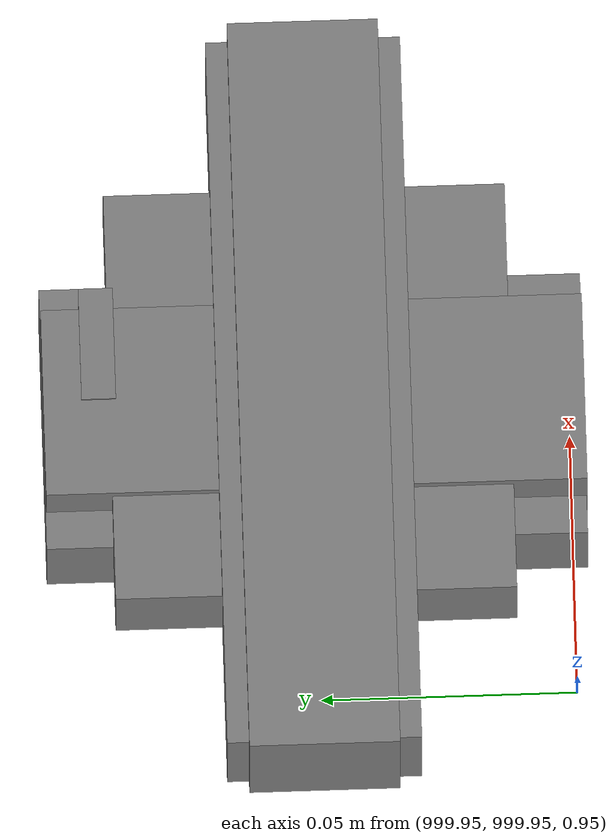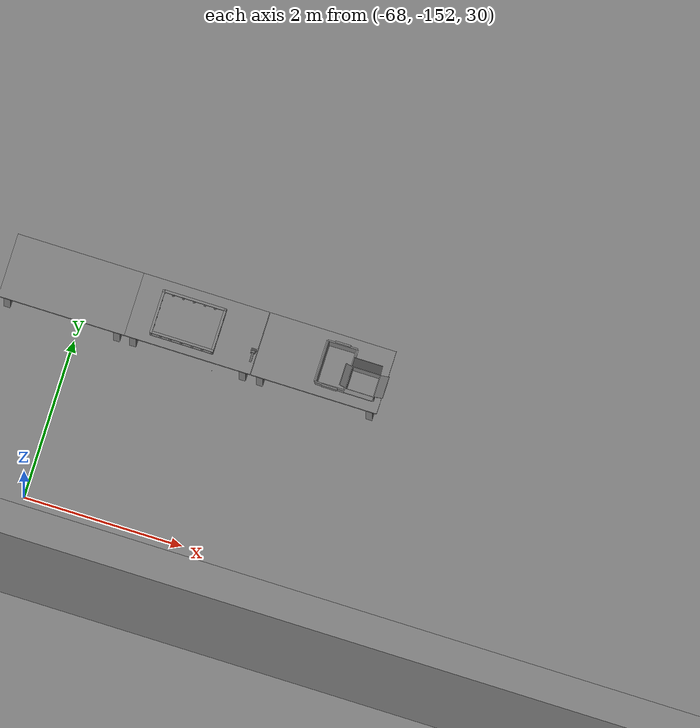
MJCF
<mujoco>
    <option gravity="0.000000000 0.000000000 -9.810000420" timestep="0.0049999999" integrator="implicitfast" density="1.225" viscosity="1.8000001e-05" noslip_iterations="10" iterations="100" sdf_iterations="50">
        <flag multiccd="disable"/>
    </option>
    <size memory="1000M"/>
    <compiler coordinate="local"/>
    <worldbody>
        <light cutoff="30" pos="0 1 1" dir="0 -1 -2"/>
        <light cutoff="30" pos="0 -1 1" dir="0 1 -2"/>
        <body pos="1000.000000000 1000.000000000 1.000000000" euler="0.000000000 0.000000000 180.000000000" name="openloong_gripper_2f85_fix_base_usda_wifi_box">
            <geom contype="1" conaffinity="1" density="1000" type="box" material="" rgba="0.500000000 0.500000000 0.500000000 1.000000000" solimp="0.899999976 0.949999988 0.001000000" friction="1.000000000 0.005000000 0.000100000" solref="0.020000000 1.000000000" margin="0" condim="3" group="0" pos="0.000000000 0.000000000 0.058978677" quat="0.000000000 0.000000047 0.000000000 1.000000000" size="0.068499997 0.018999999 0.059000000" name="openloong_gripper_2f85_fix_base_usda_geom_9D6D84C8_6115_49F3_A3A6_C89437AFA83F"/>
            <freejoint name="openloong_gripper_2f85_fix_base_usda_wifi_box_joint"/>
            <site size="0.005000000 0.005000000 0.005000000" rgba="0.500000000 0.500000000 0.500000000 1.000000000" pos="0.000000000 0.000000000 0.000000000" quat="0.999961913 0.008726500 0.000000000 0.000000000" group="0" type="sphere" name="openloong_gripper_2f85_fix_base_usda_wifi_boxsite"/>
        </body>
        <body pos="1000.000000000 1000.000000000 1.000000000" euler="0.000000000 0.000000000 180.000000000" name="openloong_gripper_2f85_fix_base_usda_cpu_fan">
            <geom contype="1" conaffinity="1" density="1000" type="box" material="" rgba="0.500000000 0.500000000 0.500000000 1.000000000" solimp="0.899999976 0.949999988 0.001000000" friction="1.000000000 0.005000000 0.000100000" solref="0.020000000 1.000000000" margin="0" condim="3" group="0" pos="0.000000000 0.000000000 0.070034981" quat="0.000000000 0.000000000 0.000000000 1.000000000" size="0.070700005 0.014699999 0.070700005" name="openloong_gripper_2f85_fix_base_usda_geom_EFB9EC42_AC53_4B5B_A3CF_8A85252401DC"/>
            <freejoint name="openloong_gripper_2f85_fix_base_usda_cpu_fan_joint"/>
            <site size="0.005000000 0.005000000 0.005000000" rgba="0.500000000 0.500000000 0.500000000 1.000000000" pos="0.000000000 0.000000000 0.000000000" quat="0.999961913 0.008726535 0.000000000 0.000000000" group="0" type="sphere" name="openloong_gripper_2f85_fix_base_usda_cpu_fancsite"/>
        </body>
        <body pos="-65.939895630 -149.472473145 31.169195175" euler="-31.372121811 74.205902100 -147.525665283" mocap="true" name="spotlight6_SpotLight"/>
        <body pos="-66.261711121 -148.873641968 31.165166855" euler="-175.662689209 46.481422424 -44.570873260" mocap="true" name="spotlight3_SpotLight"/>
        <body pos="1000.000000000 1000.000000000 1.000000000" euler="0.000011953 0.000005123 -179.999984741" name="openloong_gripper_2f85_fix_base_usda_intel_box">
            <geom contype="1" conaffinity="1" density="1000" type="box" material="" rgba="0.500000000 0.500000000 0.500000000 1.000000000" solimp="0.899999976 0.949999988 0.001000000" friction="1.000000000 0.005000000 0.000100000" solref="0.020000000 1.000000000" margin="0" condim="3" group="0" pos="0.000000000 -0.000067139 0.000082284" quat="0.707106709 0.000000225 0.000000253 0.707106650" size="0.052800003 0.025300000 0.052800003" name="openloong_gripper_2f85_fix_base_usda_geom_97F53B70_A5F4_457B_8721_FAB96E2F57FB"/>
            <freejoint name="openloong_gripper_2f85_fix_base_usda_intel_box_joint"/>
            <site size="0.005000000 0.005000000 0.005000000" rgba="0.500000000 0.500000000 0.500000000 1.000000000" pos="0.000000000 0.000000000 0.000000000" quat="0.999961913 0.008726500 0.000000000 0.000000000" group="0" type="sphere" name="openloong_gripper_2f85_fix_base_usda_intel_boxsite"/>
        </body>
        <body pos="1000.000000000 1000.000000000 1.000000000" euler="0.000000000 0.000000000 180.000000000" name="openloong_gripper_2f85_fix_base_usda_battery_01">
            <geom contype="1" conaffinity="1" density="1000" type="box" material="" rgba="0.500000000 0.500000000 0.500000000 1.000000000" solimp="0.899999976 0.949999988 0.001000000" friction="1.000000000 0.005000000 0.000100000" solref="0.020000000 1.000000000" margin="0" condim="3" group="0" pos="-0.011123657 -0.041940309 0.101691343" quat="1.000000000 0.000000000 0.000000000 0.000000000" size="0.010800000 0.003375000 0.004725000" name="openloong_gripper_2f85_fix_base_usda_geom_B4999081_36A3_42EA_AA1A_20D951F5E400"/>
            <geom contype="1" conaffinity="1" density="1000" type="box" material="" rgba="0.500000000 0.500000000 0.500000000 1.000000000" solimp="0.899999976 0.949999988 0.001000000" friction="1.000000000 0.005000000 0.000100000" solref="0.020000000 1.000000000" margin="0" condim="3" group="0" pos="-0.010876465 -0.044247437 0.047066893" quat="0.998702705 -0.050920475 0.000000000 0.000000000" size="0.009450001 0.002700000 0.024975000" name="openloong_gripper_2f85_fix_base_usda_geom_5BB8A204_B779_4A82_981E_75AADE32B6AD"/>
            <geom contype="1" conaffinity="1" density="1000" type="box" material="" rgba="0.500000000 0.500000000 0.500000000 1.000000000" solimp="0.899999976 0.949999988 0.001000000" friction="1.000000000 0.005000000 0.000100000" solref="0.020000000 1.000000000" margin="0" condim="3" group="0" pos="-0.001235962 -0.000659180 0.047381196" quat="1.000000000 0.000000000 0.000000000 0.000000000" size="0.039420001 0.039150000 0.047250003" name="openloong_gripper_2f85_fix_base_usda_geom_944F3108_ED13_46D5_8973_518E9F8E6C62"/>
            <geom contype="1" conaffinity="1" density="1000" type="box" material="" rgba="0.500000000 0.500000000 0.500000000 1.000000000" solimp="0.899999976 0.949999988 0.001000000" friction="1.000000000 0.005000000 0.000100000" solref="0.020000000 1.000000000" margin="0" condim="3" group="0" pos="-0.010876465 -0.039138794 0.009851727" quat="1.000000000 0.000000000 0.000000000 0.000000000" size="0.009450001 0.010800000 0.013500000" name="openloong_gripper_2f85_fix_base_usda_geom_883250ED_A183_481A_A2B1_CDA801ABC6F9"/>
            <geom contype="1" conaffinity="1" density="1000" type="box" material="" rgba="0.500000000 0.500000000 0.500000000 1.000000000" solimp="0.899999976 0.949999988 0.001000000" friction="1.000000000 0.005000000 0.000100000" solref="0.020000000 1.000000000" margin="0" condim="3" group="0" pos="-0.010876465 -0.041528322 0.071508206" quat="1.000000000 0.000000000 0.000000000 0.000000000" size="0.009450001 0.002700000 0.027000001" name="openloong_gripper_2f85_fix_base_usda_geom_D7091A44_6001_43B4_A09D_E6D10B00690D"/>
            <freejoint name="openloong_gripper_2f85_fix_base_usda_battery_01_joint"/>
            <site size="0.005000000 0.005000000 0.005000000" rgba="0.500000000 0.500000000 0.500000000 1.000000000" pos="0.000000000 0.000000000 0.000000000" quat="0.999961913 0.008726500 0.000000000 0.000000000" group="0" type="sphere" name="openloong_gripper_2f85_fix_base_usda_battery_01site"/>
        </body>
        <body pos="1000.000000000 999.999938965 1.000000000" euler="0.000000000 0.000000000 180.000000000" name="openloong_gripper_2f85_fix_base_usda_intelcore_i5">
            <geom contype="1" conaffinity="1" density="1000" type="box" material="" rgba="0.500000000 0.500000000 0.500000000 1.000000000" solimp="0.899999976 0.949999988 0.001000000" friction="1.000000000 0.005000000 0.000100000" solref="0.020000000 1.000000000" margin="0" condim="3" group="0" pos="0.000000000 0.000000000 0.051722717" quat="0.707106709 0.000000000 0.000000000 -0.707106769" size="0.052800000 0.018080002 0.052800000" name="openloong_gripper_2f85_fix_base_usda_geom_52CF8AEC_6A4A_4DDB_987C_2520718DFEC0"/>
            <freejoint name="openloong_gripper_2f85_fix_base_usda_intelcore_i5_joint"/>
            <site size="0.005000000 0.005000000 0.005000000" rgba="0.500000000 0.500000000 0.500000000 1.000000000" pos="0.000000000 0.000000000 0.000000000" quat="0.999961913 0.008726534 0.000000000 0.000000000" group="0" type="sphere" name="openloong_gripper_2f85_fix_base_usda_intelcore_i5site"/>
        </body>
        <body pos="-66.180641174 -149.172302246 31.168159485" euler="-85.177642822 -10.697707176 102.183059692" mocap="true" name="spotlight4_SpotLight"/>
        <body pos="-64.866622925 -149.383972168 30.183746338" euler="89.999984741 89.999946594 0.000000000" name="openloong_gripper_2f85_fix_base_usda_bluebox_01">
            <geom contype="1" conaffinity="1" density="1000" type="box" material="" rgba="0.500000000 0.500000000 0.500000000 1.000000000" solimp="0.899999976 0.949999988 0.001000000" friction="1.000000000 0.005000000 0.000100000" solref="0.020000000 1.000000000" margin="0" condim="3" group="0" pos="0.276580811 0.187225342 0.000068665" quat="0.707106948 0.000077471 0.707106352 0.000077486" size="0.100000001 0.057999998 0.010000000" name="openloong_gripper_2f85_fix_base_usda_geom_2E049E06_C1BE_40C0_8CBF_95ECA0973C25"/>
            <geom contype="1" conaffinity="1" density="1000" type="box" material="" rgba="0.500000000 0.500000000 0.500000000 1.000000000" solimp="0.899999976 0.949999988 0.001000000" friction="1.000000000 0.005000000 0.000100000" solref="0.020000000 1.000000000" margin="0" condim="3" group="0" pos="0.000000000 0.002883911 0.000000000" quat="0.999999881 0.000000000 0.000000000 0.000000000" size="0.254000008 0.003000000 0.172000006" name="openloong_gripper_2f85_fix_base_usda_geom_9AFEBD40_2FDD_4FD7_91DB_044F3D1EC522"/>
            <geom contype="1" conaffinity="1" density="1000" type="box" material="" rgba="0.500000000 0.500000000 0.500000000 1.000000000" solimp="0.899999976 0.949999988 0.001000000" friction="1.000000000 0.005000000 0.000100000" solref="0.020000000 1.000000000" margin="0" condim="3" group="0" pos="0.000000000 0.124874115 0.173484802" quat="0.999796331 0.020176515 -0.000000015 0.000000030" size="0.259999990 0.119999997 0.007000000" name="openloong_gripper_2f85_fix_base_usda_geom_191A2C88_82FB_4EFF_A16D_56465F8DEB44"/>
            <geom contype="1" conaffinity="1" density="1000" type="box" material="" rgba="0.500000000 0.500000000 0.500000000 1.000000000" solimp="0.899999976 0.949999988 0.001000000" friction="1.000000000 0.005000000 0.000100000" solref="0.020000000 1.000000000" margin="0" condim="3" group="0" pos="0.000000000 0.124874115 -0.173469543" quat="0.999796331 -0.020176545 -0.000000015 0.000000000" size="0.259999990 0.119999997 0.007000000" name="openloong_gripper_2f85_fix_base_usda_geom_55F57105_9890_4E5D_B566_39472E71BF70"/>
            <geom contype="1" conaffinity="1" density="1000" type="box" material="" rgba="0.500000000 0.500000000 0.500000000 1.000000000" solimp="0.899999976 0.949999988 0.001000000" friction="1.000000000 0.005000000 0.000100000" solref="0.020000000 1.000000000" margin="0" condim="3" group="0" pos="0.000000000 0.214008331 0.188980103" quat="0.999912977 0.013176724 0.000000015 0.000000000" size="0.259999990 0.029999999 0.012500000" name="openloong_gripper_2f85_fix_base_usda_geom_9E335665_F94F_4C01_B77A_5F5C8DB8FFC0"/>
            <geom contype="1" conaffinity="1" density="1000" type="box" material="" rgba="0.500000000 0.500000000 0.500000000 1.000000000" solimp="0.899999976 0.949999988 0.001000000" friction="1.000000000 0.005000000 0.000100000" solref="0.020000000 1.000000000" margin="0" condim="3" group="0" pos="-0.258361816 0.125289917 0.001876831" quat="0.702796936 -0.020792112 0.710783124 0.020769298" size="0.189999998 0.119999997 0.009000000" name="openloong_gripper_2f85_fix_base_usda_geom_3B6605EB_AD2C_4543_9083_CB5E7146BA19"/>
            <geom contype="1" conaffinity="1" density="1000" type="box" material="" rgba="0.500000000 0.500000000 0.500000000 1.000000000" solimp="0.899999976 0.949999988 0.001000000" friction="1.000000000 0.005000000 0.000100000" solref="0.020000000 1.000000000" margin="0" condim="3" group="0" pos="0.000000000 0.214008331 -0.188980103" quat="0.999912977 -0.013176769 0.000000030 0.000000015" size="0.259999990 0.029999999 0.012500000" name="openloong_gripper_2f85_fix_base_usda_geom_19FE14C0_E5FA_4A0B_8F31_72A8D6B1013D"/>
            <geom contype="1" conaffinity="1" density="1000" type="box" material="" rgba="0.500000000 0.500000000 0.500000000 1.000000000" solimp="0.899999976 0.949999988 0.001000000" friction="1.000000000 0.005000000 0.000100000" solref="0.020000000 1.000000000" margin="0" condim="3" group="0" pos="-0.276611328 0.187225342 0.000068665" quat="0.707106650 0.000077441 0.707106709 0.000077456" size="0.100000001 0.057999998 0.010000000" name="openloong_gripper_2f85_fix_base_usda_geom_F4FBC3D3_A6A4_40C5_9D47_A14657F8C8B7"/>
            <geom contype="1" conaffinity="1" density="1000" type="box" material="" rgba="0.500000000 0.500000000 0.500000000 1.000000000" solimp="0.899999976 0.949999988 0.001000000" friction="1.000000000 0.005000000 0.000100000" solref="0.020000000 1.000000000" margin="0" condim="3" group="0" pos="0.258331299 0.125289917 0.001876831" quat="0.702851415 0.018856421 0.710823774 -0.019329369" size="0.189999998 0.119999997 0.009000000" name="openloong_gripper_2f85_fix_base_usda_geom_F884FDA6_0268_4615_BEB9_39394D0C2887"/>
            <freejoint name="openloong_gripper_2f85_fix_base_usda_bluebox_01_joint"/>
            <site size="0.005000000 0.005000000 0.005000000" rgba="0.500000000 0.500000000 0.500000000 1.000000000" pos="0.000000000 0.000000000 0.000000000" quat="0.999961913 0.008726534 0.000000000 0.000000000" group="0" type="sphere" name="openloong_gripper_2f85_fix_base_usda_bluebox_01site"/>
        </body>
        <body pos="-64.496299744 -149.491867065 30.235729218" euler="0.000000000 0.000000000 89.999946594" name="openloong_gripper_2f85_fix_base_usda_cardboardbox_01">
            <geom contype="1" conaffinity="1" density="1000" type="box" material="" rgba="0.500000000 0.500000000 0.500000000 1.000000000" solimp="0.899999976 0.949999988 0.001000000" friction="1.000000000 0.005000000 0.000100000" solref="0.020000000 1.000000000" margin="0" condim="3" group="0" pos="-0.003166199 -0.004086494 0.005052090" quat="1.000000000 0.000000000 0.000000000 0.000000000" size="0.142499998 0.177500010 0.005000000" name="openloong_gripper_2f85_fix_base_usda_geom_0C7351AE_D6FD_4AD9_913E_C5EC05299F63"/>
            <geom contype="1" conaffinity="1" density="1000" type="box" material="" rgba="0.500000000 0.500000000 0.500000000 1.000000000" solimp="0.899999976 0.949999988 0.001000000" friction="1.000000000 0.005000000 0.000100000" solref="0.020000000 1.000000000" margin="0" condim="3" group="0" pos="-0.003166199 0.170316696 0.150570869" quat="1.000000000 0.000000000 0.000000000 0.000000000" size="0.142499998 0.005000000 0.149999991" name="openloong_gripper_2f85_fix_base_usda_geom_F066A538_94A4_4E58_B396_272D9CC3E30F"/>
            <geom contype="1" conaffinity="1" density="1000" type="box" material="" rgba="0.500000000 0.500000000 0.500000000 1.000000000" solimp="0.899999976 0.949999988 0.001000000" friction="1.000000000 0.005000000 0.000100000" solref="0.020000000 1.000000000" margin="0" condim="3" group="0" pos="-0.147399902 -0.005307198 0.150570869" quat="1.000000000 0.000000000 0.000000000 0.000000000" size="0.005000000 0.177500010 0.149999991" name="openloong_gripper_2f85_fix_base_usda_geom_8A43BD74_D233_42C1_9732_B4430ECAAE70"/>
            <geom contype="1" conaffinity="1" density="1000" type="box" material="" rgba="0.500000000 0.500000000 0.500000000 1.000000000" solimp="0.899999976 0.949999988 0.001000000" friction="1.000000000 0.005000000 0.000100000" solref="0.020000000 1.000000000" margin="0" condim="3" group="0" pos="0.140275955 -0.005307198 0.150570869" quat="1.000000000 0.000000000 0.000000000 0.000000000" size="0.005000000 0.177500010 0.149999991" name="openloong_gripper_2f85_fix_base_usda_geom_F9833635_5C36_4836_BAD3_EDF12AF2344C"/>
            <geom contype="1" conaffinity="1" density="1000" type="box" material="" rgba="0.500000000 0.500000000 0.500000000 1.000000000" solimp="0.899999976 0.949999988 0.001000000" friction="1.000000000 0.005000000 0.000100000" solref="0.020000000 1.000000000" margin="0" condim="3" group="0" pos="-0.003166199 -0.181550980 0.150570869" quat="1.000000000 0.000000000 0.000000000 0.000000000" size="0.142499998 0.005000000 0.149999991" name="openloong_gripper_2f85_fix_base_usda_geom_6558F4B5_4729_4C12_BDE4_49EDA02489B1"/>
            <freejoint name="openloong_gripper_2f85_fix_base_usda_cardboardbox_01_joint"/>
            <site size="0.005000000 0.005000000 0.005000000" rgba="0.500000000 0.500000000 0.500000000 1.000000000" pos="0.000000000 0.000000000 0.000000000" quat="0.999961913 0.008726535 0.000000000 0.000000000" group="0" type="sphere" name="openloong_gripper_2f85_fix_base_usda_site_9F7E412D_3294_4634_9C99_CE3D813093FF"/>
            <body pos="0.139160156 -0.004048347 0.301930904" euler="-179.999954224 49.383502960 179.999954224" name="openloong_gripper_2f85_fix_base_usda_A1_006">
                <geom contype="1" conaffinity="1" density="1000" type="box" material="" rgba="0.500000000 0.500000000 0.500000000 1.000000000" solimp="0.899999976 0.949999988 0.001000000" friction="1.000000000 0.005000000 0.000100000" solref="0.020000000 1.000000000" margin="0" condim="3" group="0" pos="-0.071587563 0.000009537 0.001745224" quat="0.999999881 0.000000000 0.000000000 0.000000000" size="0.071249999 0.179999992 0.002500000" name="openloong_gripper_2f85_fix_base_usda_geom_2DE83A45_6D8E_439E_A299_ECB1CD23AF58"/>
                <joint armature="0" stiffness="0.07" damping="0.0099999998" axis="0.000000 1.000000 0.000000" type="hinge" name="openloong_gripper_2f85_fix_base_usda_A1_006"/>
            </body>
            <body pos="-0.145902634 -0.004086494 0.301938057" euler="-180.000000000 -60.000011444 -180.000000000" name="openloong_gripper_2f85_fix_base_usda_A2_006">
                <geom contype="1" conaffinity="1" density="1000" type="box" material="" rgba="0.500000000 0.500000000 0.500000000 1.000000000" solimp="0.899999976 0.949999988 0.001000000" friction="1.000000000 0.005000000 0.000100000" solref="0.020000000 1.000000000" margin="0" condim="3" group="0" pos="0.071268082 0.000009537 0.002717972" quat="0.000002921 0.000000000 -0.000000030 0.999999881" size="0.071249999 0.179999992 0.002500000" name="openloong_gripper_2f85_fix_base_usda_geom_41FC2F52_CBEF_4A18_BA8D_A4F32AACAD32"/>
                <joint armature="0" stiffness="0.07" damping="0.0099999998" axis="0.000000 1.000000 0.000000" type="hinge" name="openloong_gripper_2f85_fix_base_usda_A2_006"/>
            </body>
            <body pos="-0.003385544 0.175991058 0.301930904" euler="-125.858116150 -0.000004561 0.000002331" name="openloong_gripper_2f85_fix_base_usda_B2_006">
                <geom contype="1" conaffinity="1" density="1000" type="box" material="" rgba="0.500000000 0.500000000 0.500000000 1.000000000" solimp="0.899999976 0.949999988 0.001000000" friction="1.000000000 0.005000000 0.000100000" solref="0.020000000 1.000000000" margin="0" condim="3" group="0" pos="0.000009537 -0.070939064 -0.002470016" quat="0.999614120 0.027776197 -0.000000015 0.000000030" size="0.137500003 0.064999998 0.005000000" name="openloong_gripper_2f85_fix_base_usda_geom_E6943935_1328_4B67_BA58_27F025145B9B"/>
                <joint armature="0" stiffness="0.07" damping="0.0099999998" axis="1.000000 0.000000 0.000000" type="hinge" name="openloong_gripper_2f85_fix_base_usda_B2_006"/>
            </body>
            <body pos="-0.003385544 -0.184140205 0.301938057" euler="147.805557251 0.000000000 0.000000000" name="openloong_gripper_2f85_fix_base_usda_B1_006">
                <geom contype="1" conaffinity="1" density="1000" type="box" material="" rgba="0.500000000 0.500000000 0.500000000 1.000000000" solimp="0.899999976 0.949999988 0.001000000" friction="1.000000000 0.005000000 0.000100000" solref="0.020000000 1.000000000" margin="0" condim="3" group="0" pos="-0.000028610 0.070202351 -0.002703667" quat="0.999614179 -0.027776167 0.000000000 0.000000000" size="0.137500003 0.064999998 0.005000000" name="openloong_gripper_2f85_fix_base_usda_geom_5043740C_77CE_42D0_B16E_C6DD15E92A77"/>
                <joint armature="0" stiffness="0.07" damping="0.0099999998" axis="1.000000 0.000000 0.000000" type="hinge" name="openloong_gripper_2f85_fix_base_usda_B1_006"/>
            </body>
        </body>
        <body pos="-65.882858276 -149.481979370 30.229999542" euler="-64.487716675 0.000000000 0.000000000" name="openloong_gripper_2f85_fix_base_usda_Barcode">
            <geom contype="1" conaffinity="1" density="1000" type="box" material="" rgba="0.500000000 0.500000000 0.500000000 1.000000000" solimp="0.899999976 0.949999988 0.001000000" friction="1.000000000 0.005000000 0.000100000" solref="0.020000000 1.000000000" margin="0" condim="3" group="0" pos="0.000000000 0.013038635 0.001419067" quat="0.000000000 0.000000000 0.000000000 1.000000119" size="0.034000002 0.010000000 0.017999999" name="openloong_gripper_2f85_fix_base_usda_geom_E1934348_BF9C_4DB3_8A44_89F92A1E0FAB"/>
            <geom contype="1" conaffinity="1" density="1000" type="box" material="" rgba="0.500000000 0.500000000 0.500000000 1.000000000" solimp="0.899999976 0.949999988 0.001000000" friction="1.000000000 0.005000000 0.000100000" solref="0.020000000 1.000000000" margin="0" condim="3" group="0" pos="0.000000000 -0.035301208 -0.007095337" quat="0.000000000 0.000000000 -0.043619365 0.999048233" size="0.028999999 0.010000000 0.020000000" name="openloong_gripper_2f85_fix_base_usda_geom_229CEC3B_4083_4420_9289_C09AD322B6DC"/>
            <geom contype="1" conaffinity="1" density="1000" type="box" material="" rgba="0.500000000 0.500000000 0.500000000 1.000000000" solimp="0.899999976 0.949999988 0.001000000" friction="1.000000000 0.005000000 0.000100000" solref="0.020000000 1.000000000" margin="0" condim="3" group="0" pos="0.000000000 -0.043411255 -0.011749268" quat="0.922262907 0.386563420 0.000000000 0.000000000" size="0.026000001 0.010000000 0.020000000" name="openloong_gripper_2f85_fix_base_usda_geom_962E0C09_13EB_4E49_81D7_7DA5AA392C83"/>
            <geom contype="1" conaffinity="1" density="1000" type="box" material="" rgba="0.500000000 0.500000000 0.500000000 1.000000000" solimp="0.899999976 0.949999988 0.001000000" friction="1.000000000 0.005000000 0.000100000" solref="0.020000000 1.000000000" margin="0" condim="3" group="0" pos="0.000000000 -0.016967773 -0.031860352" quat="0.000000000 0.000000000 0.000000000 1.000000119" size="0.008000000 0.010000000 0.013000000" name="openloong_gripper_2f85_fix_base_usda_geom_64C23EF0_B383_4B20_84F7_DDCEDECAFFB3"/>
            <geom contype="1" conaffinity="1" density="1000" type="box" material="" rgba="0.500000000 0.500000000 0.500000000 1.000000000" solimp="0.899999976 0.949999988 0.001000000" friction="1.000000000 0.005000000 0.000100000" solref="0.020000000 1.000000000" margin="0" condim="3" group="0" pos="0.000000000 -0.001869202 0.000312805" quat="0.953716993 0.300705761 0.000000000 0.000000000" size="0.032000002 0.010000000 0.018999999" name="openloong_gripper_2f85_fix_base_usda_geom_96EB83D6_2A8E_493C_ADAE_0E593AD2D5D2"/>
            <geom contype="1" conaffinity="1" density="1000" type="box" material="" rgba="0.500000000 0.500000000 0.500000000 1.000000000" solimp="0.899999976 0.949999988 0.001000000" friction="1.000000000 0.005000000 0.000100000" solref="0.020000000 1.000000000" margin="0" condim="3" group="0" pos="0.000000000 -0.019531250 -0.003173828" quat="0.953716993 0.300705761 0.000000000 0.000000000" size="0.030999999 0.010000000 0.020000000" name="openloong_gripper_2f85_fix_base_usda_geom_EB21C4CC_CC3D_4678_A91B_F122BDC2D9B5"/>
            <geom contype="1" conaffinity="1" density="1000" type="box" material="" rgba="0.500000000 0.500000000 0.500000000 1.000000000" solimp="0.899999976 0.949999988 0.001000000" friction="1.000000000 0.005000000 0.000100000" solref="0.020000000 1.000000000" margin="0" condim="3" group="0" pos="0.000000000 -0.035301208 -0.007095337" quat="0.953716993 0.300705761 0.000000000 0.000000000" size="0.028999999 0.010000000 0.020000000" name="openloong_gripper_2f85_fix_base_usda_geom_1EEB720C_F05B_4671_ADD9_7314CEEC18F0"/>
            <geom contype="1" conaffinity="1" density="1000" type="box" material="" rgba="0.500000000 0.500000000 0.500000000 1.000000000" solimp="0.899999976 0.949999988 0.001000000" friction="1.000000000 0.005000000 0.000100000" solref="0.020000000 1.000000000" margin="0" condim="3" group="0" pos="0.000000000 -0.042617798 -0.071121216" quat="0.000000000 0.000000000 0.000000000 1.000000119" size="0.013000000 0.021000000 0.059999999" name="openloong_gripper_2f85_fix_base_usda_geom_F500F5FF_08B2_4D5B_8C1C_B627BF3E82C1"/>
            <freejoint name="openloong_gripper_2f85_fix_base_usda_Barcode_joint"/>
            <site size="0.005000000 0.005000000 0.005000000" rgba="0.500000000 0.500000000 0.500000000 1.000000000" pos="0.000000000 0.000000000 0.000000000" quat="1.000000000 0.000000000 0.000000000 0.000000000" group="0" type="sphere" name="openloong_gripper_2f85_fix_base_usda_Barcode_site"/>
        </body>
        <body pos="-66.745018005 -149.392349243 30.184000015" euler="0.000000000 0.000000000 89.999946594" name="[22333148436850]_Basket_01">
            <geom contype="1" conaffinity="1" density="1000" type="box" material="" rgba="0.500000000 0.500000000 0.500000000 1.000000000" solimp="0.899999976 0.949999988 0.001000000" friction="1.000000000 0.005000000 0.000100000" solref="0.020000000 1.000000000" margin="0" condim="3" group="0" pos="-0.052425385 0.389207840 0.089787483" quat="0.707107008 0.000000000 0.000000000 0.707106411" size="0.014249999 0.014249999 0.059999999" name="[22333148436850]_geom_F3DC6E46_ACA7_4FDF_A512_D108619482D0"/>
            <geom contype="1" conaffinity="1" density="1000" type="box" material="" rgba="0.500000000 0.500000000 0.500000000 1.000000000" solimp="0.899999976 0.949999988 0.001000000" friction="1.000000000 0.005000000 0.000100000" solref="0.020000000 1.000000000" margin="0" condim="3" group="0" pos="0.264015198 -0.133043289 0.089787483" quat="0.707107008 0.000000000 0.000000000 0.707106411" size="0.014249999 0.014249999 0.059999999" name="[22333148436850]_geom_6977778E_7C7A_4104_8052_823D815F996F"/>
            <geom contype="1" conaffinity="1" density="1000" type="box" material="" rgba="0.500000000 0.500000000 0.500000000 1.000000000" solimp="0.899999976 0.949999988 0.001000000" friction="1.000000000 0.005000000 0.000100000" solref="0.020000000 1.000000000" margin="0" condim="3" group="0" pos="-0.264015198 -0.265548706 0.089793205" quat="0.707107008 0.000000000 0.000000000 0.707106411" size="0.014249999 0.014249999 0.059999999" name="[22333148436850]_geom_73D84E61_B98D_4E7E_A30D_A4B5C089FC6E"/>
            <geom contype="1" conaffinity="1" density="1000" type="box" material="" rgba="0.500000000 0.500000000 0.500000000 1.000000000" solimp="0.899999976 0.949999988 0.001000000" friction="1.000000000 0.005000000 0.000100000" solref="0.020000000 1.000000000" margin="0" condim="3" group="0" pos="-0.160263062 -0.389322281 0.089793205" quat="0.707107008 0.000000000 0.000000000 0.707106411" size="0.014249999 0.014249999 0.059999999" name="[22333148436850]_geom_19F64AC3_E073_4B3D_BCBF_181F7D974ABA"/>
            <geom contype="1" conaffinity="1" density="1000" type="box" material="" rgba="0.500000000 0.500000000 0.500000000 1.000000000" solimp="0.899999976 0.949999988 0.001000000" friction="1.000000000 0.005000000 0.000100000" solref="0.020000000 1.000000000" margin="0" condim="3" group="0" pos="0.162265778 -0.389322281 0.089787483" quat="0.707107008 0.000000000 0.000000000 0.707106411" size="0.014249999 0.014249999 0.059999999" name="[22333148436850]_geom_34F3909E_4E73_4B46_BC1A_02FFCD52D787"/>
            <geom contype="1" conaffinity="1" density="1000" type="box" material="" rgba="0.500000000 0.500000000 0.500000000 1.000000000" solimp="0.899999976 0.949999988 0.001000000" friction="1.000000000 0.005000000 0.000100000" solref="0.020000000 1.000000000" margin="0" condim="3" group="0" pos="0.264015198 0.389207840 0.089787483" quat="0.707107008 0.000000000 0.000000000 0.707106411" size="0.014249999 0.014249999 0.059999999" name="[22333148436850]_geom_1920159A_83C8_429E_A9DB_EF93B242BC86"/>
            <geom contype="1" conaffinity="1" density="1000" type="box" material="" rgba="0.500000000 0.500000000 0.500000000 1.000000000" solimp="0.899999976 0.949999988 0.001000000" friction="1.000000000 0.005000000 0.000100000" solref="0.020000000 1.000000000" margin="0" condim="3" group="0" pos="-0.264015198 -0.133043289 0.089793205" quat="0.707107008 0.000000000 0.000000000 0.707106411" size="0.014249999 0.014249999 0.059999999" name="[22333148436850]_geom_206C4A9F_51FF_4E1A_9F17_D085687FECC5"/>
            <geom contype="1" conaffinity="1" density="1000" type="box" material="" rgba="0.500000000 0.500000000 0.500000000 1.000000000" solimp="0.899999976 0.949999988 0.001000000" friction="1.000000000 0.005000000 0.000100000" solref="0.020000000 1.000000000" margin="0" condim="3" group="0" pos="-0.264026642 0.269256592 0.089793205" quat="0.707107008 0.000000000 0.000000000 0.707106411" size="0.014249999 0.014249999 0.059999999" name="[22333148436850]_geom_61B2EB10_93A0_476C_9E0B_9B447D464968"/>
            <geom contype="1" conaffinity="1" density="1000" type="box" material="" rgba="0.500000000 0.500000000 0.500000000 1.000000000" solimp="0.899999976 0.949999988 0.001000000" friction="1.000000000 0.005000000 0.000100000" solref="0.020000000 1.000000000" margin="0" condim="3" group="0" pos="0.054462433 0.389207840 0.089787483" quat="0.707107008 0.000000000 0.000000000 0.707106411" size="0.014249999 0.014249999 0.059999999" name="[22333148436850]_geom_EAACEA1C_D66D_417A_B7AF_5971E8F3066D"/>
            <geom contype="1" conaffinity="1" density="1000" type="box" material="" rgba="0.500000000 0.500000000 0.500000000 1.000000000" solimp="0.899999976 0.949999988 0.001000000" friction="1.000000000 0.005000000 0.000100000" solref="0.020000000 1.000000000" margin="0" condim="3" group="0" pos="0.054462433 -0.389322281 0.089787483" quat="0.707107008 0.000000000 0.000000000 0.707106411" size="0.014249999 0.014249999 0.059999999" name="[22333148436850]_geom_654EDC7B_1432_4F0C_B22C_EA6C3EBC4172"/>
            <geom contype="1" conaffinity="1" density="1000" type="box" material="" rgba="0.500000000 0.500000000 0.500000000 1.000000000" solimp="0.899999976 0.949999988 0.001000000" friction="1.000000000 0.005000000 0.000100000" solref="0.020000000 1.000000000" margin="0" condim="3" group="0" pos="0.264015198 0.269256592 0.089793205" quat="0.707107008 0.000000000 0.000000000 0.707106411" size="0.014249999 0.014249999 0.059999999" name="[22333148436850]_geom_F36AEDB7_4CBD_49A3_99D2_D9BC209573DC"/>
            <geom contype="1" conaffinity="1" density="1000" type="box" material="" rgba="0.500000000 0.500000000 0.500000000 1.000000000" solimp="0.899999976 0.949999988 0.001000000" friction="1.000000000 0.005000000 0.000100000" solref="0.020000000 1.000000000" margin="0" condim="3" group="0" pos="0.264015198 -0.389322281 0.089787483" quat="0.707107008 0.000000000 0.000000000 0.707106411" size="0.014249999 0.014249999 0.059999999" name="[22333148436850]_geom_944BE6F7_A2E2_43A0_B06F_C0B1688B1AA9"/>
            <geom contype="1" conaffinity="1" density="1000" type="box" material="" rgba="0.500000000 0.500000000 0.500000000 1.000000000" solimp="0.899999976 0.949999988 0.001000000" friction="1.000000000 0.005000000 0.000100000" solref="0.020000000 1.000000000" margin="0" condim="3" group="0" pos="0.000000000 0.000000000 0.015998840" quat="0.707107008 0.000000000 0.000000000 0.707106411" size="0.403499991 0.279000014 0.015750000" name="[22333148436850]_geom_BC16A0DD_62A5_4769_B01E_04BC180AC9E2"/>
            <geom contype="1" conaffinity="1" density="1000" type="box" material="" rgba="0.500000000 0.500000000 0.500000000 1.000000000" solimp="0.899999976 0.949999988 0.001000000" friction="1.000000000 0.005000000 0.000100000" solref="0.020000000 1.000000000" margin="0" condim="3" group="0" pos="0.000000000 -0.389476776 0.163619041" quat="0.707107008 0.000000000 0.000000000 0.707106411" size="0.015000000 0.277500004 0.015750000" name="[22333148436850]_geom_7FB683DC_D294_4003_ADDF_32D71170A578"/>
            <geom contype="1" conaffinity="1" density="1000" type="box" material="" rgba="0.500000000 0.500000000 0.500000000 1.000000000" solimp="0.899999976 0.949999988 0.001000000" friction="1.000000000 0.005000000 0.000100000" solref="0.020000000 1.000000000" margin="0" condim="3" group="0" pos="0.162265778 0.389207840 0.089787483" quat="0.707107008 0.000000000 0.000000000 0.707106411" size="0.014249999 0.014249999 0.059999999" name="[22333148436850]_geom_CE649862_0DD9_4D5A_9FA7_63449B81C733"/>
            <geom contype="1" conaffinity="1" density="1000" type="box" material="" rgba="0.500000000 0.500000000 0.500000000 1.000000000" solimp="0.899999976 0.949999988 0.001000000" friction="1.000000000 0.005000000 0.000100000" solref="0.020000000 1.000000000" margin="0" condim="3" group="0" pos="0.000000000 0.389471054 0.163619041" quat="0.707107008 0.000000000 0.000000000 0.707106411" size="0.015000000 0.277500004 0.015750000" name="[22333148436850]_geom_ECB8CC85_7FF9_4B01_BD4B_A770866354F4"/>
            <geom contype="1" conaffinity="1" density="1000" type="box" material="" rgba="0.500000000 0.500000000 0.500000000 1.000000000" solimp="0.899999976 0.949999988 0.001000000" friction="1.000000000 0.005000000 0.000100000" solref="0.020000000 1.000000000" margin="0" condim="3" group="0" pos="-0.263511658 0.000000000 0.163619041" quat="0.707107008 0.000000000 0.000000000 0.707106411" size="0.403499991 0.015000000 0.015750000" name="[22333148436850]_geom_A62840EC_F9DD_4CEC_BDC7_4EF1FD858E04"/>
            <geom contype="1" conaffinity="1" density="1000" type="box" material="" rgba="0.500000000 0.500000000 0.500000000 1.000000000" solimp="0.899999976 0.949999988 0.001000000" friction="1.000000000 0.005000000 0.000100000" solref="0.020000000 1.000000000" margin="0" condim="3" group="0" pos="-0.264015198 0.141334534 0.089793205" quat="0.707107008 0.000000000 0.000000000 0.707106411" size="0.014249999 0.014249999 0.059999999" name="[22333148436850]_geom_92A655EB_596D_4F07_8A2A_3B20E50ABE2C"/>
            <geom contype="1" conaffinity="1" density="1000" type="box" material="" rgba="0.500000000 0.500000000 0.500000000 1.000000000" solimp="0.899999976 0.949999988 0.001000000" friction="1.000000000 0.005000000 0.000100000" solref="0.020000000 1.000000000" margin="0" condim="3" group="0" pos="0.264015198 -0.265548706 0.089787483" quat="0.707107008 0.000000000 0.000000000 0.707106411" size="0.014249999 0.014249999 0.059999999" name="[22333148436850]_geom_B896F9F5_32BA_49BD_B583_4052D94F2CDF"/>
            <geom contype="1" conaffinity="1" density="1000" type="box" material="" rgba="0.500000000 0.500000000 0.500000000 1.000000000" solimp="0.899999976 0.949999988 0.001000000" friction="1.000000000 0.005000000 0.000100000" solref="0.020000000 1.000000000" margin="0" condim="3" group="0" pos="-0.160263062 0.389207840 0.089787483" quat="0.707107008 0.000000000 0.000000000 0.707106411" size="0.014249999 0.014249999 0.059999999" name="[22333148436850]_geom_B96192EC_309D_44AF_976B_B49BD397C74E"/>
            <geom contype="1" conaffinity="1" density="1000" type="box" material="" rgba="0.500000000 0.500000000 0.500000000 1.000000000" solimp="0.899999976 0.949999988 0.001000000" friction="1.000000000 0.005000000 0.000100000" solref="0.020000000 1.000000000" margin="0" condim="3" group="0" pos="-0.052425385 -0.389322281 0.089787483" quat="0.707107008 0.000000000 0.000000000 0.707106411" size="0.014249999 0.014249999 0.059999999" name="[22333148436850]_geom_1579F0F8_2E8E_4E36_83D5_F04C68D8564A"/>
            <geom contype="1" conaffinity="1" density="1000" type="box" material="" rgba="0.500000000 0.500000000 0.500000000 1.000000000" solimp="0.899999976 0.949999988 0.001000000" friction="1.000000000 0.005000000 0.000100000" solref="0.020000000 1.000000000" margin="0" condim="3" group="0" pos="-0.264026642 -0.389322281 0.089793205" quat="0.707107008 0.000000000 0.000000000 0.707106411" size="0.014249999 0.014249999 0.059999999" name="[22333148436850]_geom_27B7925D_3BBA_4456_A75A_E258FEF71C7B"/>
            <geom contype="1" conaffinity="1" density="1000" type="box" material="" rgba="0.500000000 0.500000000 0.500000000 1.000000000" solimp="0.899999976 0.949999988 0.001000000" friction="1.000000000 0.005000000 0.000100000" solref="0.020000000 1.000000000" margin="0" condim="3" group="0" pos="0.264015198 0.141334534 0.089787483" quat="0.707107008 0.000000000 0.000000000 0.707106411" size="0.014249999 0.014249999 0.059999999" name="[22333148436850]_geom_33523AB2_439F_4ADD_9472_5E0F5AD40F49"/>
            <geom contype="1" conaffinity="1" density="1000" type="box" material="" rgba="0.500000000 0.500000000 0.500000000 1.000000000" solimp="0.899999976 0.949999988 0.001000000" friction="1.000000000 0.005000000 0.000100000" solref="0.020000000 1.000000000" margin="0" condim="3" group="0" pos="-0.264015198 0.389207840 0.089793205" quat="0.707107008 0.000000000 0.000000000 0.707106411" size="0.014249999 0.014249999 0.059999999" name="[22333148436850]_geom_97C9B792_CFB8_48ED_AC85_806CAF9895B6"/>
            <geom contype="1" conaffinity="1" density="1000" type="box" material="" rgba="0.500000000 0.500000000 0.500000000 1.000000000" solimp="0.899999976 0.949999988 0.001000000" friction="1.000000000 0.005000000 0.000100000" solref="0.020000000 1.000000000" margin="0" condim="3" group="0" pos="0.264015198 0.004480362 0.089787483" quat="0.707107008 0.000000000 0.000000000 0.707106411" size="0.014249999 0.014249999 0.059999999" name="[22333148436850]_geom_B01241AF_D4FE_47E3_80DC_AB59B855C843"/>
            <geom contype="1" conaffinity="1" density="1000" type="box" material="" rgba="0.500000000 0.500000000 0.500000000 1.000000000" solimp="0.899999976 0.949999988 0.001000000" friction="1.000000000 0.005000000 0.000100000" solref="0.020000000 1.000000000" margin="0" condim="3" group="0" pos="0.263694763 -0.000011444 0.163619041" quat="0.707107008 0.000000000 0.000000000 0.707106411" size="0.403499991 0.015000000 0.015750000" name="[22333148436850]_geom_8ED1C0E6_2152_4598_89D4_62AB9D6A9FE8"/>
            <geom contype="1" conaffinity="1" density="1000" type="box" material="" rgba="0.500000000 0.500000000 0.500000000 1.000000000" solimp="0.899999976 0.949999988 0.001000000" friction="1.000000000 0.005000000 0.000100000" solref="0.020000000 1.000000000" margin="0" condim="3" group="0" pos="-0.264015198 0.004480362 0.089793205" quat="0.707107008 0.000000000 0.000000000 0.707106411" size="0.014249999 0.014249999 0.059999999" name="[22333148436850]_geom_16D79B47_5B7A_410C_9B76_D5510F8F88AE"/>
            <freejoint name="[22333148436850]_joint_B0B4F44C_634C_4FF6_9073_5768234BF7B2"/>
        </body>
        <body pos="0.000000000 0.000000000 0.000000000" euler="0.000000000 0.000000000 0.000000000" name="Static Objects_Static Objects">
            <geom contype="1" conaffinity="1" density="1000" type="box" material="" rgba="0.500000000 0.500000000 0.500000000 1.000000000" solimp="0.899999976 0.949999988 0.001000000" friction="1.000000000 0.005000000 0.000100000" solref="0.020000000 1.000000000" margin="0" condim="3" group="0" pos="-67.544113159 -149.365814209 29.727830887" quat="0.500000417 0.499999970 0.499999553 0.499999970" size="0.381000012 0.319999993 0.041000001" name="Static Objects_geom_D03D8F4A_44C2_40E8_92AA_10A3DCEF1863"/>
            <geom contype="1" conaffinity="1" density="1000" type="box" material="" rgba="0.500000000 0.500000000 0.500000000 1.000000000" solimp="0.899999976 0.949999988 0.001000000" friction="1.000000000 0.005000000 0.000100000" solref="0.020000000 1.000000000" margin="0" condim="3" group="0" pos="-68.239501953 -149.365814209 30.086868286" quat="0.500000417 0.499999970 0.499999553 0.499999970" size="0.370999992 0.039500002 0.745000005" name="Static Objects_geom_0724EFEC_1824_4B80_B2BC_61DC05DA7BA5"/>
            <geom contype="1" conaffinity="1" density="1000" type="box" material="" rgba="0.500000000 0.500000000 0.500000000 1.000000000" solimp="0.899999976 0.949999988 0.001000000" friction="1.000000000 0.005000000 0.000100000" solref="0.020000000 1.000000000" margin="0" condim="3" group="0" pos="-68.239501953 -149.365814209 30.147235870" quat="0.500000417 0.499999970 0.499999553 0.499999970" size="0.400000006 0.022000000 0.800000012" name="Static Objects_geom_3686736D_FF56_4BA4_8D75_1B7C44C7C419"/>
            <geom contype="1" conaffinity="1" density="1000" type="box" material="" rgba="0.500000000 0.500000000 0.500000000 1.000000000" solimp="0.899999976 0.949999988 0.001000000" friction="1.000000000 0.005000000 0.000100000" solref="0.020000000 1.000000000" margin="0" condim="3" group="0" pos="-68.934890747 -149.365814209 29.727830887" quat="0.500000417 0.499999970 0.499999553 0.499999970" size="0.381000012 0.319999993 0.041000001" name="Static Objects_geom_A11B652E_E331_4E13_BC57_AEF026F7024C"/>
            <geom contype="1" conaffinity="1" density="1000" type="box" material="" rgba="0.500000000 0.500000000 0.500000000 1.000000000" solimp="0.899999976 0.949999988 0.001000000" friction="1.000000000 0.005000000 0.000100000" solref="0.020000000 1.000000000" margin="0" condim="3" group="0" pos="-68.239501953 -149.365814209 29.561563492" quat="0.500000417 0.499999970 0.499999553 0.499999970" size="0.020000000 0.022000000 0.660000026" name="Static Objects_geom_F0194B05_7163_479E_AF3D_8F5C70F16212"/>
            <geom contype="1" conaffinity="1" density="1000" type="box" material="" rgba="0.500000000 0.500000000 0.500000000 1.000000000" solimp="0.899999976 0.949999988 0.001000000" friction="1.000000000 0.005000000 0.000100000" solref="0.020000000 1.000000000" margin="0" condim="3" group="0" pos="-65.945671082 -149.365814209 29.727830887" quat="0.500000417 0.499999970 0.499999553 0.499999970" size="0.381000012 0.319999993 0.041000001" name="Static Objects_geom_AA5064F7_DFCA_44FC_B0C1_6D69F1085225"/>
            <geom contype="1" conaffinity="1" density="1000" type="box" material="" rgba="0.500000000 0.500000000 0.500000000 1.000000000" solimp="0.899999976 0.949999988 0.001000000" friction="1.000000000 0.005000000 0.000100000" solref="0.020000000 1.000000000" margin="0" condim="3" group="0" pos="-66.641059875 -149.365814209 30.086868286" quat="0.500000417 0.499999970 0.499999553 0.499999970" size="0.370999992 0.039500002 0.745000005" name="Static Objects_geom_D4A0A909_1546_4A35_82B3_3C65A38ECBAB"/>
            <geom contype="1" conaffinity="1" density="1000" type="box" material="" rgba="0.500000000 0.500000000 0.500000000 1.000000000" solimp="0.899999976 0.949999988 0.001000000" friction="1.000000000 0.005000000 0.000100000" solref="0.020000000 1.000000000" margin="0" condim="3" group="0" pos="-66.641059875 -149.365814209 30.147235870" quat="0.500000417 0.499999970 0.499999553 0.499999970" size="0.400000006 0.022000000 0.800000012" name="Static Objects_geom_DA5DDD1B_B31C_464B_A7DD_AC0747A9DA37"/>
            <geom contype="1" conaffinity="1" density="1000" type="box" material="" rgba="0.500000000 0.500000000 0.500000000 1.000000000" solimp="0.899999976 0.949999988 0.001000000" friction="1.000000000 0.005000000 0.000100000" solref="0.020000000 1.000000000" margin="0" condim="3" group="0" pos="-67.336448669 -149.365814209 29.727830887" quat="0.500000417 0.499999970 0.499999553 0.499999970" size="0.381000012 0.319999993 0.041000001" name="Static Objects_geom_FAB9ED54_E780_47F2_8436_A650434B1ABC"/>
            <geom contype="1" conaffinity="1" density="1000" type="box" material="" rgba="0.500000000 0.500000000 0.500000000 1.000000000" solimp="0.899999976 0.949999988 0.001000000" friction="1.000000000 0.005000000 0.000100000" solref="0.020000000 1.000000000" margin="0" condim="3" group="0" pos="-66.641059875 -149.365814209 29.561563492" quat="0.500000417 0.499999970 0.499999553 0.499999970" size="0.020000000 0.022000000 0.660000026" name="Static Objects_geom_33C3055F_6694_45AE_BA08_1713BA117176"/>
            <geom contype="1" conaffinity="1" density="1000" type="box" material="" rgba="0.500000000 0.500000000 0.500000000 1.000000000" solimp="0.899999976 0.949999988 0.001000000" friction="1.000000000 0.005000000 0.000100000" solref="0.020000000 1.000000000" margin="0" condim="3" group="0" pos="-64.338577271 -149.365814209 29.727830887" quat="0.500000417 0.499999970 0.499999553 0.499999970" size="0.381000012 0.319999993 0.041000001" name="Static Objects_geom_95BA36B6_0311_4DA0_9F3D_516F2DC271A2"/>
            <geom contype="1" conaffinity="1" density="1000" type="box" material="" rgba="0.500000000 0.500000000 0.500000000 1.000000000" solimp="0.899999976 0.949999988 0.001000000" friction="1.000000000 0.005000000 0.000100000" solref="0.020000000 1.000000000" margin="0" condim="3" group="0" pos="-65.033966064 -149.365814209 30.086868286" quat="0.500000417 0.499999970 0.499999553 0.499999970" size="0.370999992 0.039500002 0.745000005" name="Static Objects_geom_E6FA3551_30C2_474A_A092_8C05DA9383FE"/>
            <geom contype="1" conaffinity="1" density="1000" type="box" material="" rgba="0.500000000 0.500000000 0.500000000 1.000000000" solimp="0.899999976 0.949999988 0.001000000" friction="1.000000000 0.005000000 0.000100000" solref="0.020000000 1.000000000" margin="0" condim="3" group="0" pos="-65.033966064 -149.365814209 30.147235870" quat="0.500000417 0.499999970 0.499999553 0.499999970" size="0.400000006 0.022000000 0.800000012" name="Static Objects_geom_AFE515F2_6737_4158_AE9F_82CD220F25BE"/>
            <geom contype="1" conaffinity="1" density="1000" type="box" material="" rgba="0.500000000 0.500000000 0.500000000 1.000000000" solimp="0.899999976 0.949999988 0.001000000" friction="1.000000000 0.005000000 0.000100000" solref="0.020000000 1.000000000" margin="0" condim="3" group="0" pos="-65.729354858 -149.365814209 29.727830887" quat="0.500000417 0.499999970 0.499999553 0.499999970" size="0.381000012 0.319999993 0.041000001" name="Static Objects_geom_754F2480_E7B1_44FD_96CE_8A6EADA8A982"/>
            <geom contype="1" conaffinity="1" density="1000" type="box" material="" rgba="0.500000000 0.500000000 0.500000000 1.000000000" solimp="0.899999976 0.949999988 0.001000000" friction="1.000000000 0.005000000 0.000100000" solref="0.020000000 1.000000000" margin="0" condim="3" group="0" pos="-65.033966064 -149.365814209 29.561563492" quat="0.500000417 0.499999970 0.499999553 0.499999970" size="0.020000000 0.022000000 0.660000026" name="Static Objects_geom_DC9C3195_0F15_4414_BABF_CA9B4E9E6CF1"/>
            <geom contype="1" conaffinity="1" density="1000" type="box" material="" rgba="0.500000000 0.500000000 0.500000000 1.000000000" solimp="0.899999976 0.949999988 0.001000000" friction="1.000000000 0.005000000 0.000100000" solref="0.020000000 1.000000000" margin="0" condim="3" group="0" pos="-61.754566193 -137.853729248 33.906845093" quat="0.707107067 0.000000000 0.000000000 0.707106471" size="0.759999990 0.759999990 4.500000000" name="Static Objects_geom_467050EF_8189_4470_A64E_5FC6BC385443"/>
            <geom contype="1" conaffinity="1" density="1000" type="box" material="" rgba="0.500000000 0.500000000 0.500000000 1.000000000" solimp="0.899999976 0.949999988 0.001000000" friction="1.000000000 0.005000000 0.000100000" solref="0.020000000 1.000000000" margin="0" condim="3" group="0" pos="-57.511135101 -144.927108765 31.707921982" quat="1.000000000 0.000000000 0.000000000 0.000000000" size="0.200000003 8.000000000 2.299999952" name="Static Objects_geom_73FB11B4_1751_4B8F_9438_230B3F8B817E"/>
            <geom contype="1" conaffinity="1" density="1000" type="box" material="" rgba="0.500000000 0.500000000 0.500000000 1.000000000" solimp="0.899999976 0.949999988 0.001000000" friction="1.000000000 0.005000000 0.000100000" solref="0.020000000 1.000000000" margin="0" condim="3" group="0" pos="-80.517646790 -157.574050903 31.688196182" quat="0.707107067 0.000000000 0.000000000 0.707106471" size="0.600000024 0.600000024 2.299999952" name="Static Objects_geom_1442A674_41F1_45A1_AE6F_C00751DE0584"/>
            <geom contype="1" conaffinity="1" density="1000" type="box" material="" rgba="0.500000000 0.500000000 0.500000000 1.000000000" solimp="0.899999976 0.949999988 0.001000000" friction="1.000000000 0.005000000 0.000100000" solref="0.020000000 1.000000000" margin="0" condim="3" group="0" pos="-80.711044312 -147.414932251 31.666158676" quat="1.000000000 0.000000000 0.000000000 0.000000000" size="0.200000003 10.000000000 2.299999952" name="Static Objects_geom_929D6165_15B1_4858_8057_C40BC39E0DD1"/>
            <geom contype="1" conaffinity="1" density="1000" type="box" material="" rgba="0.500000000 0.500000000 0.500000000 1.000000000" solimp="0.899999976 0.949999988 0.001000000" friction="1.000000000 0.005000000 0.000100000" solref="0.020000000 1.000000000" margin="0" condim="3" group="0" pos="-57.687217712 -137.434692383 31.688196182" quat="0.707107067 0.000000000 0.000000000 0.707106471" size="0.600000024 0.600000024 2.299999952" name="Static Objects_geom_6661C00B_E69D_431F_BC47_C082105D2533"/>
            <geom contype="1" conaffinity="1" density="1000" type="box" material="" rgba="0.500000000 0.500000000 0.500000000 1.000000000" solimp="0.899999976 0.949999988 0.001000000" friction="1.000000000 0.005000000 0.000100000" solref="0.020000000 1.000000000" margin="0" condim="3" group="0" pos="-69.537033081 -140.263229370 31.714921951" quat="0.707107067 0.000000000 0.000000000 0.707106471" size="0.759999990 4.500000000 2.299999952" name="Static Objects_geom_6C953F78_4136_4EC4_9D77_DBB2F47C4820"/>
            <geom contype="1" conaffinity="1" density="1000" type="box" material="" rgba="0.500000000 0.500000000 0.500000000 1.000000000" solimp="0.899999976 0.949999988 0.001000000" friction="1.000000000 0.005000000 0.000100000" solref="0.020000000 1.000000000" margin="0" condim="3" group="0" pos="-80.073638916 -137.853713989 33.906845093" quat="0.707107067 0.000000000 0.000000000 0.707106471" size="0.759999990 0.759999990 4.500000000" name="Static Objects_geom_DF758DAF_EA43_42C0_88F2_215B18D201D5"/>
            <geom contype="1" conaffinity="1" density="1000" type="box" material="" rgba="0.500000000 0.500000000 0.500000000 1.000000000" solimp="0.899999976 0.949999988 0.001000000" friction="1.000000000 0.005000000 0.000100000" solref="0.020000000 1.000000000" margin="0" condim="3" group="0" pos="-73.406707764 -155.734664917 31.707921982" quat="1.000000000 0.000000000 0.000000000 0.000000000" size="0.200000003 3.000000000 2.299999952" name="Static Objects_geom_63FAC7BD_6772_4185_A501_0F762AB60148"/>
            <geom contype="1" conaffinity="1" density="1000" type="box" material="" rgba="0.500000000 0.500000000 0.500000000 1.000000000" solimp="0.899999976 0.949999988 0.001000000" friction="1.000000000 0.005000000 0.000100000" solref="0.020000000 1.000000000" margin="0" condim="3" group="0" pos="-68.497543335 -137.448257446 31.707921982" quat="0.707107067 0.000000000 0.000000000 0.707106471" size="0.200000003 14.000000000 2.299999952" name="Static Objects_geom_FED63528_F43F_48C0_A92F_7133AEF6FF20"/>
            <geom contype="1" conaffinity="1" density="1000" type="cylinder" material="" rgba="0.500000000 0.500000000 0.500000000 1.000000000" solimp="0.899999976 0.949999988 0.001000000" friction="1.000000000 0.005000000 0.000100000" solref="0.020000000 1.000000000" margin="0" condim="3" group="0" pos="-68.868522644 -142.134506226 31.711090088" quat="0.707107067 0.000000000 0.000000000 0.707106471" size="0.509999990 2.299999952 1.000000000" name="Static Objects_geom_2AC1459F_0E43_4454_91E9_665D0E5EF254"/>
            <geom contype="1" conaffinity="1" density="1000" type="plane" material="" rgba="0.500000000 0.500000000 0.500000000 1.000000000" solimp="0.899999976 0.949999988 0.001000000" friction="1.000000000 0.005000000 0.000100000" solref="0.020000000 1.000000000" margin="0" condim="3" group="0" pos="-72.873703003 -147.131927490 29.409669876" quat="1.000000000 0.000000000 0.000000000 0.000000000" size="18.000000000 14.000000000 1.000000000" name="Static Objects_geom_13D2C06A_02B9_48AE_99C9_9F330BA04323"/>
            <geom contype="1" conaffinity="1" density="1000" type="box" material="" rgba="0.500000000 0.500000000 0.500000000 1.000000000" solimp="0.899999976 0.949999988 0.001000000" friction="1.000000000 0.005000000 0.000100000" solref="0.020000000 1.000000000" margin="0" condim="3" group="0" pos="-79.943580627 -157.782272339 31.707921982" quat="0.707107067 0.000000000 0.000000000 0.707106471" size="0.200000003 7.000000000 2.299999952" name="Static Objects_geom_00E1F2CB_8E60_4C02_95FA_49963779EB62"/>
            <geom contype="1" conaffinity="1" density="1000" type="box" material="" rgba="0.500000000 0.500000000 0.500000000 1.000000000" solimp="0.899999976 0.949999988 0.001000000" friction="1.000000000 0.005000000 0.000100000" solref="0.020000000 1.000000000" margin="0" condim="3" group="0" pos="-65.421028137 -152.903442383 31.707921982" quat="0.707107067 0.000000000 0.000000000 0.707106471" size="0.200000003 7.800000191 2.299999952" name="Static Objects_geom_F43A7709_8275_4DD9_B6BD_4181F7B62F0C"/>
            <geom contype="1" conaffinity="1" density="1000" type="box" material="" rgba="0.500000000 0.500000000 0.500000000 1.000000000" solimp="0.899999976 0.949999988 0.001000000" friction="1.000000000 0.005000000 0.000100000" solref="0.020000000 1.000000000" margin="0" condim="3" group="0" pos="-74.776908875 -149.964416504 31.688196182" quat="1.000000000 0.000000000 0.000000000 0.000000000" size="0.600000024 0.409999996 2.299999952" name="Static Objects_geom_FAF54450_8F86_4C28_9AA4_1D42D08A8332"/>
            <geom contype="1" conaffinity="1" density="1000" type="cylinder" material="" rgba="0.500000000 0.500000000 0.500000000 1.000000000" solimp="0.899999976 0.949999988 0.001000000" friction="1.000000000 0.005000000 0.000100000" solref="0.020000000 1.000000000" margin="0" condim="3" group="0" pos="-60.161884308 -142.134506226 31.711090088" quat="0.707107067 0.000000000 0.000000000 0.707106471" size="0.509999990 2.299999952 1.000000000" name="Static Objects_geom_9FAFBA90_11F4_46A5_93B6_E246F07A7E85"/>
            <geom contype="1" conaffinity="1" density="1000" type="cylinder" material="" rgba="0.500000000 0.500000000 0.500000000 1.000000000" solimp="0.899999976 0.949999988 0.001000000" friction="1.000000000 0.005000000 0.000100000" solref="0.020000000 1.000000000" margin="0" condim="3" group="0" pos="-75.382453918 -149.963455200 31.711090088" quat="0.707107067 0.000000000 0.000000000 0.707106471" size="0.409999996 2.299999952 1.000000000" name="Static Objects_geom_6EBB7E75_61D2_4183_BC66_450EAB6CD90F"/>
            <geom contype="1" conaffinity="1" density="1000" type="cylinder" material="" rgba="0.500000000 0.500000000 0.500000000 1.000000000" solimp="0.899999976 0.949999988 0.001000000" friction="1.000000000 0.005000000 0.000100000" solref="0.020000000 1.000000000" margin="0" condim="3" group="0" pos="-74.154960632 -149.963455200 31.711090088" quat="0.707107067 0.000000000 0.000000000 0.707106471" size="0.409999996 2.299999952 1.000000000" name="Static Objects_geom_35733792_56C2_494A_A3BD_ED8FFFA03521"/>
            <geom contype="1" conaffinity="1" density="1000" type="cylinder" material="" rgba="0.500000000 0.500000000 0.500000000 1.000000000" solimp="0.899999976 0.949999988 0.001000000" friction="1.000000000 0.005000000 0.000100000" solref="0.020000000 1.000000000" margin="0" condim="3" group="0" pos="-77.566612244 -142.134506226 31.711090088" quat="0.707107067 0.000000000 0.000000000 0.707106471" size="0.509999990 2.299999952 1.000000000" name="Static Objects_geom_53E7536A_EA8D_400F_B758_63B858D96A24"/>
        </body>
        <body pos="-66.291030884 -149.869689941 29.018842697" euler="0.000000000 0.000000000 89.999946594" mocap="true" name="openloong_gripper_2f85_fix_base_usda_leftHandMocap"/>
        <body pos="-66.291030884 -149.869689941 29.018842697" euler="0.000000000 0.000000000 89.999946594" mocap="true" name="openloong_gripper_2f85_fix_base_usda_rightHandMocap"/>
        <body pos="-66.291030884 -149.869689941 30.218843460" euler="0.000000000 0.000000000 89.999946594" name="openloong_gripper_2f85_fix_base_usda_base_link">
            <geom contype="1" conaffinity="1" density="1000" type="mesh" material="" rgba="0.783999979 0.783999979 0.783999979 1.000000000" solimp="0.899999976 0.949999988 0.001000000" friction="1.000000000 0.005000000 0.000100000" solref="0.020000000 1.000000000" margin="0" condim="3" group="3" mesh="base_link" pos="0.000000000 0.000000000 0.000000000" quat="1.000000000 0.000000000 0.000000000 0.000000000" size="1.000000000 1.000000000 1.000000000" name="openloong_gripper_2f85_fix_base_usda__geom_7_514BF3AA_40F9_49E4_A55D_0C313151802B"/>
            <site size="0.005000000 0.005000000 0.005000000" rgba="0.500000000 0.500000000 0.500000000 1.000000000" pos="0.000000000 0.000000000 0.000000000" quat="1.000000000 0.000000000 0.000000000 0.000000000" group="0" type="sphere" name="openloong_gripper_2f85_fix_base_usda_imu"/>
            <inertial mass="22.447001" pos="-0.005664100 -0.001336700 0.238289997" diaginertia="0.374352545 0.277180195 0.220617250" quat="0.999247074 0.035235517 -0.015086859 0.006023135"/>
            <body pos="0.000000000 0.000000000 0.299997330" euler="0.000000000 0.000000000 0.000000000" name="openloong_gripper_2f85_fix_base_usda_dummy_body">
                <geom contype="1" conaffinity="1" density="1000" type="sphere" material="" rgba="0.783999979 0.783999979 0.783999979 1.000000000" solimp="0.899999976 0.949999988 0.001000000" friction="1.000000000 0.005000000 0.000100000" solref="0.020000000 1.000000000" margin="0" condim="3" group="3" pos="0.000000000 0.000000000 0.000000000" quat="1.000000000 0.000000000 0.000000000 0.000000000" size="0.010000000 0.000000000 0.000000000" name="openloong_gripper_2f85_fix_base_usda__geom_8_54E36BFA_8E42_4CDD_B58D_E081763EE8F9"/>
                <joint armature="0.0099999998" stiffness="0" damping="0.1" axis="0.000000 0.000000 1.000000" type="hinge" name="openloong_gripper_2f85_fix_base_usda_dummy_joint"/>
                <site size="0.010000000 0.005000000 0.005000000" rgba="0.500000000 0.500000000 0.500000000 1.000000000" pos="0.000000000 0.000000000 0.000000000" quat="1.000000000 0.000000000 0.000000000 0.000000000" group="3" type="sphere" name="openloong_gripper_2f85_fix_base_usda_dummy_site"/>
            </body>
            <body pos="0.009002686 0.000000000 0.406400681" euler="0.000000000 0.000000000 0.000000000" name="openloong_gripper_2f85_fix_base_usda_Link_head_yaw">
                <geom contype="1" conaffinity="1" density="1000" type="mesh" material="" rgba="0.783999979 0.783999979 0.783999979 1.000000000" solimp="0.899999976 0.949999988 0.001000000" friction="1.000000000 0.005000000 0.000100000" solref="0.020000000 1.000000000" margin="0" condim="3" group="3" mesh="Link_head_yaw" pos="0.000000000 0.000000000 0.000000000" quat="1.000000000 0.000000000 0.000000000 0.000000000" size="1.000000000 1.000000000 1.000000000" name="openloong_gripper_2f85_fix_base_usda__geom_10_B73635C9_F239_4452_B81A_782BD942B94B"/>
                <inertial mass="0.84249002" pos="0.000000000 -0.002081400 0.044801001" diaginertia="0.000700588 0.000629000 0.000553812" quat="0.706933022 -0.015675601 0.015677100 0.706933022"/>
                <body pos="0.000000000 -0.034599304 0.048500061" euler="0.000000000 0.000000000 0.000000000" name="openloong_gripper_2f85_fix_base_usda_Link_head_pitch">
                    <geom contype="1" conaffinity="1" density="1000" type="mesh" material="" rgba="0.783999979 0.783999979 0.783999979 1.000000000" solimp="0.899999976 0.949999988 0.001000000" friction="1.000000000 0.005000000 0.000100000" solref="0.020000000 1.000000000" margin="0" condim="3" group="3" mesh="Link_head_pitch" pos="0.000000000 0.000000000 0.000000000" quat="1.000000000 0.000000000 0.000000000 0.000000000" size="1.000000000 1.000000000 1.000000000" name="openloong_gripper_2f85_fix_base_usda__geom_12_3E6D4868_9C36_4F89_A1C8_376337CA82C0"/>
                    <inertial mass="1.3943" pos="0.020569000 0.033004001 0.125000000" diaginertia="0.006381400 0.006289940 0.004481460" quat="0.973390222 0.008406822 0.228157058 0.019624906"/>
                    <body pos="0.000000000 0.029998779 0.000000000" euler="0.000000000 0.000000000 0.000000000" name="openloong_gripper_2f85_fix_base_usda_neck_center_body">
                        <site size="0.010000000 0.005000000 0.005000000" rgba="0.500000000 0.500000000 0.500000000 1.000000000" pos="0.000000000 0.000000000 0.000000000" quat="1.000000000 0.000000000 0.000000000 0.000000000" group="3" type="sphere" name="openloong_gripper_2f85_fix_base_usda_neck_center_site"/>
                        <body pos="0.020004272 0.000000000 0.149999619" euler="-0.000002229 39.998176575 -90.000205994" name="openloong_gripper_2f85_fix_base_usda_camera_head">
                            <site size="0.010000000 0.005000000 0.005000000" rgba="0.500000000 0.500000000 0.500000000 1.000000000" pos="0.000000000 0.000000000 0.000000000" quat="1.000000000 0.000000000 0.000000000 0.000000000" group="3" type="sphere" name="openloong_gripper_2f85_fix_base_usda_camera_head_site"/>
                        </body>
                    </body>
                </body>
            </body>
            <body pos="0.003997803 -0.161598206 0.392200470" euler="0.000000000 0.000000000 0.000000000" name="openloong_gripper_2f85_fix_base_usda_Link_arm_r_01">
                <geom contype="1" conaffinity="1" density="1000" type="mesh" material="" rgba="0.783999979 0.783999979 0.783999979 1.000000000" solimp="0.899999976 0.949999988 0.001000000" friction="1.000000000 0.005000000 0.000100000" solref="0.020000000 1.000000000" margin="0" condim="3" group="3" mesh="Link_arm_r_01" pos="0.000000000 0.000000000 0.000000000" quat="1.000000000 0.000000000 0.000000000 0.000000000" size="1.000000000 1.000000000 1.000000000" name="openloong_gripper_2f85_fix_base_usda__geom_14_3281470F_BE43_496D_8B12_0449CF067955"/>
                <joint armature="0.0099999998" stiffness="0" damping="1" axis="0.000000 -1.000000 0.000000" limited="true" range="-170.000015259 170.000015259" type="hinge" name="openloong_gripper_2f85_fix_base_usda_J_arm_r_01"/>
                <inertial mass="0.75641" pos="0.004494600 -0.038293999 -0.000001874" diaginertia="0.000842990 0.000803050 0.000587120" quat="-0.000163502 0.707098067 0.000812463 0.707115054"/>
                <body pos="-0.041992188 -0.041000366 0.000000000" euler="0.000000000 0.000000000 0.000000000" name="openloong_gripper_2f85_fix_base_usda_Link_arm_r_02">
                    <geom contype="1" conaffinity="1" density="1000" type="mesh" material="" rgba="0.783999979 0.783999979 0.783999979 1.000000000" solimp="0.899999976 0.949999988 0.001000000" friction="1.000000000 0.005000000 0.000100000" solref="0.020000000 1.000000000" margin="0" condim="3" group="3" mesh="Link_arm_r_02" pos="0.000000000 0.000000000 0.000000000" quat="1.000000000 0.000000000 0.000000000 0.000000000" size="1.000000000 1.000000000 1.000000000" name="openloong_gripper_2f85_fix_base_usda__geom_16_C6496F01_A2BF_48E5_A28B_20F39067F4F9"/>
                    <joint armature="0.0099999998" stiffness="0" damping="1" axis="-1.000000 0.000000 0.000000" limited="true" range="-105.000244141 105.000244141" type="hinge" name="openloong_gripper_2f85_fix_base_usda_J_arm_r_02"/>
                    <inertial mass="0.98500001" pos="0.041999999 -0.067430697 0.000000000" diaginertia="0.002262690 0.001730990 0.001154020" quat="0.500000000 0.500000000 -0.500000000 0.500000000"/>
                    <body pos="0.041992188 -0.122596741 0.000000000" euler="0.000000000 0.000000000 0.000000000" name="openloong_gripper_2f85_fix_base_usda_Link_arm_r_03">
                        <geom contype="1" conaffinity="1" density="1000" type="mesh" material="" rgba="0.783999979 0.783999979 0.783999979 1.000000000" solimp="0.899999976 0.949999988 0.001000000" friction="1.000000000 0.005000000 0.000100000" solref="0.020000000 1.000000000" margin="0" condim="3" group="3" mesh="Link_arm_r_03" pos="0.000000000 0.000000000 0.000000000" quat="1.000000000 0.000000000 0.000000000 0.000000000" size="1.000000000 1.000000000 1.000000000" name="openloong_gripper_2f85_fix_base_usda__geom_18_FD22B0C5_998B_4096_BA4D_764855C5A95F"/>
                        <joint armature="0.0099999998" stiffness="0" damping="1" axis="0.000000 -1.000000 0.000000" limited="true" range="-170.000015259 170.000015259" type="hinge" name="openloong_gripper_2f85_fix_base_usda_J_arm_r_03"/>
                        <inertial mass="0.95899999" pos="-0.001413580 -0.164663002 0.020757901" diaginertia="0.002101340 0.002064590 0.000754802" quat="0.560480952 0.454391927 -0.443732947 0.531497955"/>
                        <body pos="0.035293579 -0.177406311 0.023998260" euler="0.000000000 0.000000000 0.000000000" name="openloong_gripper_2f85_fix_base_usda_Link_arm_r_04">
                            <geom contype="1" conaffinity="1" density="1000" type="mesh" material="" rgba="0.783999979 0.783999979 0.783999979 1.000000000" solimp="0.899999976 0.949999988 0.001000000" friction="1.000000000 0.005000000 0.000100000" solref="0.020000000 1.000000000" margin="0" condim="3" group="3" mesh="Link_arm_r_04" pos="0.000000000 0.000000000 0.000000000" quat="1.000000000 0.000000000 0.000000000 0.000000000" size="1.000000000 1.000000000 1.000000000" name="openloong_gripper_2f85_fix_base_usda__geom_20_157C9DF7_9CDB_4619_A275_F5F50363CA2B"/>
                            <joint armature="0.0099999998" stiffness="0" damping="1" axis="-1.000000 0.000000 0.000000" limited="true" range="0.000000000 170.000015259" type="hinge" name="openloong_gripper_2f85_fix_base_usda_J_arm_r_04"/>
                            <inertial mass="0.60000002" pos="-0.038727000 -0.060766999 -0.021003000" diaginertia="0.001092610 0.000712422 0.000645102" quat="0.327701002 0.632602990 -0.467366993 0.523443997"/>
                            <body pos="-0.035293579 -0.103492737 -0.023998260" euler="0.000000000 0.000000000 0.000000000" name="openloong_gripper_2f85_fix_base_usda_Link_arm_r_05">
                                <geom contype="1" conaffinity="1" density="1000" type="mesh" material="" rgba="0.783999979 0.783999979 0.783999979 1.000000000" solimp="0.899999976 0.949999988 0.001000000" friction="1.000000000 0.005000000 0.000100000" solref="0.020000000 1.000000000" margin="0" condim="3" group="3" mesh="Link_arm_r_05" pos="0.000000000 0.000000000 0.000000000" quat="1.000000000 0.000000000 0.000000000 0.000000000" size="1.000000000 1.000000000 1.000000000" name="openloong_gripper_2f85_fix_base_usda__geom_22_40EC46C6_377C_429C_8C53_C88689A225C3"/>
                                <joint armature="0.0099999998" stiffness="0" damping="1" axis="0.000000 -1.000000 0.000000" limited="true" range="-170.000015259 170.000015259" type="hinge" name="openloong_gripper_2f85_fix_base_usda_J_arm_r_05"/>
                                <inertial mass="0.68976003" pos="0.000032712 -0.068658002 -0.000111780" diaginertia="0.002522510 0.002411100 0.000448695" quat="0.707660973 0.706543028 -0.002603360 0.002470550"/>
                                <body pos="-0.026489258 -0.196502686 0.000000000" euler="0.000000000 0.000000000 0.000000000" name="openloong_gripper_2f85_fix_base_usda_Link_arm_r_06">
                                    <geom contype="1" conaffinity="1" density="1000" type="mesh" material="" rgba="0.783999979 0.783999979 0.783999979 1.000000000" solimp="0.899999976 0.949999988 0.001000000" friction="1.000000000 0.005000000 0.000100000" solref="0.020000000 1.000000000" margin="0" condim="3" group="3" mesh="Link_arm_r_06" pos="0.000000000 0.000000000 0.000000000" quat="1.000000000 0.000000000 0.000000000 0.000000000" size="1.000000000 1.000000000 1.000000000" name="openloong_gripper_2f85_fix_base_usda__geom_24_D7CBD2C2_B628_434E_AC96_E00BC43B70DB"/>
                                    <joint armature="0.0099999998" stiffness="0" damping="1" axis="1.000000 0.000000 0.000000" limited="true" range="-105.000244141 105.000244141" type="hinge" name="openloong_gripper_2f85_fix_base_usda_J_arm_r_06"/>
                                    <inertial mass="0.28" pos="0.026078001 -0.000000896 0.001663700" diaginertia="0.000156930 0.000145601 0.000104979" quat="0.707080841 0.001851080 0.001883810 0.707127810"/>
                                    <body pos="0.026489258 0.000000000 0.031799316" euler="0.000000000 0.000000000 0.000000000" name="openloong_gripper_2f85_fix_base_usda_Link_arm_r_07">
                                        <geom contype="1" conaffinity="1" density="1000" type="mesh" material="" rgba="0.783999979 0.783999979 0.783999979 1.000000000" solimp="0.899999976 0.949999988 0.001000000" friction="1.000000000 0.005000000 0.000100000" solref="0.020000000 1.000000000" margin="0" condim="3" group="3" mesh="Link_arm_r_07" pos="0.000000000 0.000000000 0.000000000" quat="1.000000000 0.000000000 0.000000000 0.000000000" size="1.000000000 1.000000000 1.000000000" name="openloong_gripper_2f85_fix_base_usda__geom_26_F6BB87B0_8CCF_4218_A40D_850639D0CB0B"/>
                                        <joint armature="0.0099999998" stiffness="0" damping="1" axis="0.000000 0.000000 1.000000" limited="true" range="-60.000133514 60.000133514" type="hinge" name="openloong_gripper_2f85_fix_base_usda_J_arm_r_07"/>
                                        <inertial mass="0.61353999" pos="-0.007859000 -0.158170000 -0.027736001" diaginertia="0.003037610 0.002570910 0.000729379" quat="0.427542925 0.443532884 -0.553093910 0.560867906"/>
                                        <body pos="0.000000000 0.286994934 -0.270000458" euler="150.000350952 -0.000001649 -0.000000442" name="openloong_gripper_2f85_fix_base_usda_camera_wrist_r">
                                            <site size="0.010000000 0.005000000 0.005000000" rgba="0.500000000 0.500000000 0.500000000 1.000000000" pos="0.000000000 0.000000000 0.000000000" quat="1.000000000 0.000000000 0.000000000 0.000000000" group="3" type="sphere" name="openloong_gripper_2f85_fix_base_usda_camera_wrist_r_site"/>
                                        </body>
                                        <body pos="0.000000000 -0.220008850 -0.033002853" euler="0.000000000 0.000000000 179.999969482" name="openloong_gripper_2f85_fix_base_usda_ee_center_body_r">
                                            <site size="0.010000000 0.005000000 0.005000000" rgba="0.500000000 0.500000000 0.500000000 1.000000000" pos="0.000000000 0.000000000 0.000000000" quat="1.000000000 0.000000000 0.000000000 0.000000000" group="3" type="sphere" name="openloong_gripper_2f85_fix_base_usda_ee_center_site_r"/>
                                        </body>
                                        <body pos="0.000000000 -0.066001892 -0.031000137" euler="89.999984741 0.000000000 180.000000000" name="openloong_gripper_2f85_fix_base_usda_zbr_base_link">
                                            <geom contype="1" conaffinity="1" density="1000" type="mesh" material="" rgba="0.783999979 0.783999979 0.783999979 1.000000000" solimp="0.899999976 0.949999988 0.001000000" friction="1.000000000 0.005000000 0.000100000" solref="0.020000000 1.000000000" margin="0" condim="3" group="3" mesh="base" pos="0.000000000 0.000003815 -0.000007629" quat="1.000000000 0.000000000 0.000000000 0.000000000" size="1.000000238 1.000000238 1.000000238" name="openloong_gripper_2f85_fix_base_usda__geom_30_54E09404_9E25_486C_AF99_0F3A7EDDE68A"/>
                                            <inertial mass="0.77744102" pos="0.000000000 -0.000027039 0.035467502" diaginertia="0.000260285 0.000225381 0.000152708" quat="0.999998808 -0.001528488 0.000000000 0.000000000"/>
                                            <body pos="-0.030609138 0.004745484 0.065696731" euler="-89.999984741 -0.000000000 0.000000000" name="openloong_gripper_2f85_fix_base_usda_r_left_driver">
                                                <geom contype="1" conaffinity="1" density="1000" type="mesh" material="" rgba="0.783999979 0.783999979 0.783999979 1.000000000" solimp="0.899999976 0.949999988 0.001000000" friction="1.000000000 0.005000000 0.000100000" solref="0.020000000 1.000000000" margin="0" condim="3" group="3" mesh="driver" pos="0.030609138 0.054901138 -0.004699708" quat="0.707106829 0.707106709 0.000000000 -0.000000000" size="1.000000238 1.000000238 1.000000238" name="openloong_gripper_2f85_fix_base_usda__geom_32_EBF56A9A_2833_46EB_AE88_1D712FD3EED6"/>
                                                <joint armature="0.0049999999" stiffness="0" damping="0.1" axis="0.000000 0.000000 1.000000" limited="true" range="0.000000000 51.566200256" type="hinge" name="openloong_gripper_2f85_fix_base_usda_r_left_driver_joint"/>
                                                <inertial mass="0.0089956298" pos="0.000000000 0.017754700 0.001073140" diaginertia="0.000001724 0.000001609 0.000000322" quat="0.681301236 0.732003212 0.000000000 0.000000000"/>
                                                <body pos="-0.031402595 0.004524232 -0.010200503" euler="0.000000000 0.000000000 180.000000000" name="openloong_gripper_2f85_fix_base_usda_r_left_coupler">
                                                    <geom contype="1" conaffinity="1" density="1000" type="mesh" material="" rgba="0.783999979 0.783999979 0.783999979 1.000000000" solimp="0.899999976 0.949999988 0.001000000" friction="1.000000000 0.005000000 0.000100000" solref="0.020000000 1.000000000" margin="0" condim="3" group="3" mesh="coupler" pos="-0.062011734 -0.050354015 0.005500795" quat="0.707106829 -0.707106709 0.000000000 -0.000000000" size="1.000000238 1.000000238 1.000000238" name="openloong_gripper_2f85_fix_base_usda__geom_34_EBE3BAA1_21E5_4876_AAE1_EF0F16140CD6"/>
                                                    <inertial mass="0.0140974" pos="0.000000000 0.003012090 0.023217499" diaginertia="0.000004162 0.000003522 0.000000888" quat="0.705635548 -0.045590367 0.045590367 0.705635548"/>
                                                </body>
                                            </body>
                                            <body pos="-0.012695315 -0.012001040 0.072212234" euler="-89.999984741 -0.000000000 0.000000000" name="openloong_gripper_2f85_fix_base_usda_r_left_spring_link">
                                                <geom contype="1" conaffinity="1" density="1000" type="mesh" material="" rgba="0.783999979 0.783999979 0.783999979 1.000000000" solimp="0.899999976 0.949999988 0.001000000" friction="1.000000000 0.005000000 0.000100000" solref="0.020000000 1.000000000" margin="0" condim="3" group="3" mesh="spring_link" pos="0.012695315 0.061416641 0.012050631" quat="0.707106829 0.707106709 0.000000000 -0.000000000" size="1.000000238 1.000000238 1.000000238" name="openloong_gripper_2f85_fix_base_usda__geom_36_EBA2071F_46AE_4522_B22A_F6E2C4AAFA48"/>
                                                <joint armature="0.001" stiffness="0.050000001" damping="0.00125" axis="0.000000 0.000000 1.000000" limited="true" range="-17.000000000 51.566200256" type="hinge" name="openloong_gripper_2f85_fix_base_usda_r_left_spring_link_joint"/>
                                                <inertial mass="0.0221642" pos="-0.000000009 0.018162400 0.021265799" diaginertia="0.000008969 0.000006717 0.000002639" quat="0.663403213 -0.244737089 0.244737089 0.663403213"/>
                                                <body pos="-0.038208015 -0.042503368 0.002950669" euler="180.000000000 0.000000000 -0.002185660" name="openloong_gripper_2f85_fix_base_usda_r_left_follower">
                                                    <geom contype="1" conaffinity="1" density="1000" type="mesh" material="" rgba="0.783999979 0.783999979 0.783999979 1.000000000" solimp="0.899999976 0.949999988 0.001000000" friction="1.000000000 0.005000000 0.000100000" solref="0.020000000 1.000000000" margin="0" condim="3" group="3" mesh="tongue" pos="0.050918590 -0.103920005 -0.009099962" quat="0.707106829 -0.707106709 0.000000030 0.000000030" size="1.000000238 1.000000238 1.000000238" name="openloong_gripper_2f85_fix_base_usda__geom_40_A0DBF310_A63D_4649_B2AC_91B72097620B"/>
                                                    <geom contype="1" conaffinity="1" density="1000" type="mesh" material="" rgba="0.783999979 0.783999979 0.783999979 1.000000000" solimp="0.899999976 0.949999988 0.001000000" friction="1.000000000 0.005000000 0.000100000" solref="0.020000000 1.000000000" margin="0" condim="3" group="3" mesh="follower" pos="0.050918590 -0.103920005 -0.009099962" quat="0.707106829 -0.707106709 0.000000030 0.000000030" size="1.000000238 1.000000238 1.000000238" name="openloong_gripper_2f85_fix_base_usda__geom_39_F861B72F_1C66_4686_AAFF_131959D96EDC"/>
                                                    <joint armature="0.001" stiffness="0" damping="0.1" axis="0.000000 0.000000 1.000000" limited="true" range="-49.999961853 51.566200256" type="hinge" name="openloong_gripper_2f85_fix_base_usda_r_left_follower"/>
                                                    <inertial mass="0.0125222" pos="0.000000000 -0.011046000 0.012478600" diaginertia="0.000002674 0.000002456 0.000000602" quat="0.986436546 0.164143041 0.000000000 0.000000000"/>
                                                    <body pos="-0.037765510 -0.103912376 -0.009099962" euler="-89.999984741 0.000000000 0.000004829" name="openloong_gripper_2f85_fix_base_usda_r_left_pad">
                                                        <geom contype="1" conaffinity="1" density="1000" type="box" material="" rgba="0.550000012 0.550000012 0.550000012 1.000000000" solimp="0.949999988 0.990000010 0.001000000" friction="0.699999988 0.005000000 0.000100000" solref="0.020000000 1.000000000" margin="0" condim="3" group="3" mass="1e-06" pos="0.043243419 0.000003815 0.119995147" quat="0.999999881 0.000000000 0.000000000 0.000000000" size="0.002000001 0.011000003 0.009375002" name="openloong_gripper_2f85_fix_base_usda_r_left_pad1_B062ECCA_96A4_44DE_AAC8_F28D1D9FC333"/>
                                                        <geom contype="1" conaffinity="1" density="1000" type="box" material="" rgba="0.449999988 0.449999988 0.449999988 1.000000000" solimp="0.949999988 0.990000010 0.001000000" friction="0.600000024 0.005000000 0.000100000" solref="0.020000000 1.000000000" margin="0" condim="3" group="3" mass="1e-06" pos="0.043243419 0.000003815 0.138748199" quat="0.999999881 0.000000000 0.000000000 0.000000000" size="0.002000001 0.011000003 0.009375002" name="openloong_gripper_2f85_fix_base_usda_r_left_pad2_315EEF2D_8E0A_468F_BE7E_D49D2EEE6328"/>
                                                    </body>
                                                </body>
                                            </body>
                                            <body pos="0.030593880 -0.004753114 0.065696731" euler="89.999984741 0.000000000 180.000000000" name="openloong_gripper_2f85_fix_base_usda_r_right_driver">
                                                <geom contype="1" conaffinity="1" density="1000" type="mesh" material="" rgba="0.783999979 0.783999979 0.783999979 1.000000000" solimp="0.899999976 0.949999988 0.001000000" friction="1.000000000 0.005000000 0.000100000" solref="0.020000000 1.000000000" margin="0" condim="3" group="3" mesh="driver" pos="0.030593880 0.054901138 -0.004699708" quat="0.707106829 0.707106709 0.000000000 0.000000000" size="1.000000238 1.000000238 1.000000238" name="openloong_gripper_2f85_fix_base_usda__geom_42_53117B0F_3E2A_458D_8EC8_EEE79B3A45D9"/>
                                                <joint armature="0.0049999999" stiffness="0" damping="0.1" axis="0.000000 0.000000 1.000000" limited="true" range="0.000000000 51.566200256" type="hinge" name="openloong_gripper_2f85_fix_base_usda_r_right_driver_joint"/>
                                                <inertial mass="0.0089956298" pos="0.000000000 0.017754700 0.001073140" diaginertia="0.000001724 0.000001609 0.000000322" quat="0.681301236 0.732003212 0.000000000 0.000000000"/>
                                                <body pos="-0.031417854 0.004531861 -0.010202411" euler="0.000000000 0.000000000 180.000000000" name="openloong_gripper_2f85_fix_base_usda_r_right_coupler">
                                                    <geom contype="1" conaffinity="1" density="1000" type="mesh" material="" rgba="0.783999979 0.783999979 0.783999979 1.000000000" solimp="0.899999976 0.949999988 0.001000000" friction="1.000000000 0.005000000 0.000100000" solref="0.020000000 1.000000000" margin="0" condim="3" group="3" mesh="coupler" pos="-0.062042251 -0.050376903 0.005500795" quat="0.707106829 -0.707106709 0.000000000 0.000000000" size="1.000000238 1.000000238 1.000000238" name="openloong_gripper_2f85_fix_base_usda__geom_44_20B9650C_B360_4B40_90EE_806AD434F082"/>
                                                    <inertial mass="0.0140974" pos="0.000000000 0.003012090 0.023217499" diaginertia="0.000004162 0.000003522 0.000000888" quat="0.705635548 -0.045590367 0.045590367 0.705635548"/>
                                                </body>
                                            </body>
                                            <body pos="0.012695315 0.011997226 0.072219864" euler="89.999984741 0.000000000 180.000000000" name="openloong_gripper_2f85_fix_base_usda_r_right_spring_link">
                                                <geom contype="1" conaffinity="1" density="1000" type="mesh" material="" rgba="0.783999979 0.783999979 0.783999979 1.000000000" solimp="0.899999976 0.949999988 0.001000000" friction="1.000000000 0.005000000 0.000100000" solref="0.020000000 1.000000000" margin="0" condim="3" group="3" mesh="spring_link" pos="0.012695315 0.061424270 0.012048724" quat="0.707106829 0.707106709 0.000000000 0.000000000" size="1.000000238 1.000000238 1.000000238" name="openloong_gripper_2f85_fix_base_usda__geom_46_55934624_F37D_47A8_B022_3652047FB7F0"/>
                                                <joint armature="0.001" stiffness="0.050000001" damping="0.00125" axis="0.000000 0.000000 1.000000" limited="true" range="-17.000000000 51.566200256" type="hinge" name="openloong_gripper_2f85_fix_base_usda_r_right_spring_link_joint"/>
                                                <inertial mass="0.0221642" pos="-0.000000009 0.018162400 0.021265799" diaginertia="0.000008969 0.000006717 0.000002639" quat="0.663403213 -0.244737089 0.244737089 0.663403213"/>
                                                <body pos="-0.038208015 -0.042495739 0.002950669" euler="180.000000000 0.000000000 0.000000000" name="openloong_gripper_2f85_fix_base_usda_r_right_follower">
                                                    <geom contype="1" conaffinity="1" density="1000" type="mesh" material="" rgba="0.783999979 0.783999979 0.783999979 1.000000000" solimp="0.899999976 0.949999988 0.001000000" friction="1.000000000 0.005000000 0.000100000" solref="0.020000000 1.000000000" margin="0" condim="3" group="3" mesh="follower" pos="0.050888073 -0.103927635 -0.009099962" quat="0.707106829 -0.707106709 0.000000000 0.000000000" size="1.000000238 1.000000238 1.000000238" name="openloong_gripper_2f85_fix_base_usda__geom_50_07E595EF_3DF6_4E98_8892_E6188020EED2"/>
                                                    <geom contype="1" conaffinity="1" density="1000" type="mesh" material="" rgba="0.783999979 0.783999979 0.783999979 1.000000000" solimp="0.899999976 0.949999988 0.001000000" friction="1.000000000 0.005000000 0.000100000" solref="0.020000000 1.000000000" margin="0" condim="3" group="3" mesh="tongue" pos="0.050888073 -0.103927635 -0.009099962" quat="0.707106829 -0.707106709 0.000000000 0.000000000" size="1.000000238 1.000000238 1.000000238" name="openloong_gripper_2f85_fix_base_usda__geom_49_37C3E84F_130C_48F9_B690_7431400B766B"/>
                                                    <joint armature="0.001" stiffness="0" damping="0.1" axis="0.000000 0.000000 1.000000" limited="true" range="-49.999961853 51.566200256" type="hinge" name="openloong_gripper_2f85_fix_base_usda_r_right_follower_joint"/>
                                                    <inertial mass="0.0125222" pos="0.000000000 -0.011046000 0.012478600" diaginertia="0.000002674 0.000002456 0.000000602" quat="0.986436546 0.164143041 0.000000000 0.000000000"/>
                                                    <body pos="-0.037811287 -0.103927635 -0.009099962" euler="-89.999984741 0.000000000 0.000000000" name="openloong_gripper_2f85_fix_base_usda_r_right_pad">
                                                        <geom contype="1" conaffinity="1" density="1000" type="box" material="" rgba="0.449999988 0.449999988 0.449999988 1.000000000" solimp="0.949999988 0.990000010 0.001000000" friction="0.600000024 0.005000000 0.000100000" solref="0.020000000 1.000000000" margin="0" condim="3" group="3" mass="1e-06" pos="0.043258678 0.000000000 0.138748199" quat="1.000000000 0.000000000 0.000000000 0.000000000" size="0.002000001 0.011000003 0.009375002" name="openloong_gripper_2f85_fix_base_usda_r_right_pad2_2B2A1425_BF9D_43C2_B5C7_B58E5B0973DB"/>
                                                        <geom contype="1" conaffinity="1" density="1000" type="box" material="" rgba="0.550000012 0.550000012 0.550000012 1.000000000" solimp="0.949999988 0.990000010 0.001000000" friction="0.699999988 0.005000000 0.000100000" solref="0.020000000 1.000000000" margin="0" condim="3" group="3" mass="1e-06" pos="0.043258678 0.000003815 0.120002776" quat="1.000000000 0.000000000 0.000000000 0.000000000" size="0.002000001 0.011000003 0.009375002" name="openloong_gripper_2f85_fix_base_usda_r_right_pad1_40C94796_14C4_4AE7_BC71_5D54FC7E6435"/>
                                                    </body>
                                                </body>
                                            </body>
                                        </body>
                                    </body>
                                </body>
                            </body>
                        </body>
                    </body>
                </body>
            </body>
            <body pos="0.003997803 0.161590576 0.392200470" euler="0.000000000 0.000000000 0.000000000" name="openloong_gripper_2f85_fix_base_usda_Link_arm_l_01">
                <geom contype="1" conaffinity="1" density="1000" type="mesh" material="" rgba="0.783999979 0.783999979 0.783999979 1.000000000" solimp="0.899999976 0.949999988 0.001000000" friction="1.000000000 0.005000000 0.000100000" solref="0.020000000 1.000000000" margin="0" condim="3" group="3" mesh="Link_arm_l_01" pos="0.000000000 0.000000000 0.000000000" quat="1.000000000 0.000000000 0.000000000 0.000000000" size="1.000000000 1.000000000 1.000000000" name="openloong_gripper_2f85_fix_base_usda__geom_52_8FD40D58_E1C5_4BB7_98AC_358EE0AF8FB9"/>
                <joint armature="0.0099999998" stiffness="0" damping="1" axis="0.000000 1.000000 0.000000" limited="true" range="-170.000015259 170.000015259" type="hinge" name="openloong_gripper_2f85_fix_base_usda_J_arm_l_01"/>
                <inertial mass="0.75640601" pos="-0.004494650 0.038294200 -0.000001874" diaginertia="0.000842986 0.000803053 0.000587115" quat="-0.000812496 0.707115054 0.000163424 0.707098067"/>
                <body pos="0.042007446 0.041000366 0.000000000" euler="0.000000000 0.000000000 0.000000000" name="openloong_gripper_2f85_fix_base_usda_Link_arm_l_02">
                    <geom contype="1" conaffinity="1" density="1000" type="mesh" material="" rgba="0.783999979 0.783999979 0.783999979 1.000000000" solimp="0.899999976 0.949999988 0.001000000" friction="1.000000000 0.005000000 0.000100000" solref="0.020000000 1.000000000" margin="0" condim="3" group="3" mesh="Link_arm_l_02" pos="0.000000000 0.000000000 0.000000000" quat="1.000000000 0.000000000 0.000000000 0.000000000" size="1.000000000 1.000000000 1.000000000" name="openloong_gripper_2f85_fix_base_usda__geom_54_2EC2FA1D_9755_489F_85B6_1547D809928D"/>
                    <joint armature="0.0099999998" stiffness="0" damping="1" axis="-1.000000 0.000000 0.000000" limited="true" range="-105.000244141 105.000244141" type="hinge" name="openloong_gripper_2f85_fix_base_usda_J_arm_l_02"/>
                    <inertial mass="0.98500001" pos="-0.041999999 0.067430697 0.000000000" diaginertia="0.002262690 0.001730990 0.001154020" quat="0.500000000 0.500000000 -0.500000000 0.500000000"/>
                    <body pos="-0.042007446 0.122596741 0.000000000" euler="0.000000000 0.000000000 0.000000000" name="openloong_gripper_2f85_fix_base_usda_Link_arm_l_03">
                        <geom contype="1" conaffinity="1" density="1000" type="mesh" material="" rgba="0.783999979 0.783999979 0.783999979 1.000000000" solimp="0.899999976 0.949999988 0.001000000" friction="1.000000000 0.005000000 0.000100000" solref="0.020000000 1.000000000" margin="0" condim="3" group="3" mesh="Link_arm_l_03" pos="0.000000000 0.000000000 0.000000000" quat="1.000000000 0.000000000 0.000000000 0.000000000" size="1.000000000 1.000000000 1.000000000" name="openloong_gripper_2f85_fix_base_usda__geom_56_CD97AFCD_A896_4A88_9418_9D78BD5CE1B0"/>
                        <joint armature="0.0099999998" stiffness="0" damping="1" axis="0.000000 1.000000 0.000000" limited="true" range="-170.000015259 170.000015259" type="hinge" name="openloong_gripper_2f85_fix_base_usda_J_arm_l_03"/>
                        <inertial mass="0.95899999" pos="0.001413580 0.164663002 0.020757901" diaginertia="0.002101340 0.002064590 0.000754802" quat="0.443732947 0.531497955 -0.560480952 0.454391927"/>
                        <body pos="-0.035293579 0.177406311 0.023998260" euler="0.000000000 0.000000000 0.000000000" name="openloong_gripper_2f85_fix_base_usda_Link_arm_l_04">
                            <geom contype="1" conaffinity="1" density="1000" type="mesh" material="" rgba="0.783999979 0.783999979 0.783999979 1.000000000" solimp="0.899999976 0.949999988 0.001000000" friction="1.000000000 0.005000000 0.000100000" solref="0.020000000 1.000000000" margin="0" condim="3" group="3" mesh="Link_arm_l_04" pos="0.000000000 0.000000000 0.000000000" quat="1.000000000 0.000000000 0.000000000 0.000000000" size="1.000000000 1.000000000 1.000000000" name="openloong_gripper_2f85_fix_base_usda__geom_58_D57D359F_C593_46A7_B839_D45322860F00"/>
                            <joint armature="0.0099999998" stiffness="0" damping="1" axis="1.000000 0.000000 0.000000" limited="true" range="0.000000000 170.000015259" type="hinge" name="openloong_gripper_2f85_fix_base_usda_J_arm_l_04"/>
                            <inertial mass="0.60000002" pos="0.038727000 0.060767200 -0.021003200" diaginertia="0.001092570 0.000712419 0.000645098" quat="0.467370987 0.523440003 -0.327692002 0.632607996"/>
                            <body pos="0.035293579 0.103500366 -0.023998260" euler="0.000000000 0.000000000 0.000000000" name="openloong_gripper_2f85_fix_base_usda_Link_arm_l_05">
                                <geom contype="1" conaffinity="1" density="1000" type="mesh" material="" rgba="0.783999979 0.783999979 0.783999979 1.000000000" solimp="0.899999976 0.949999988 0.001000000" friction="1.000000000 0.005000000 0.000100000" solref="0.020000000 1.000000000" margin="0" condim="3" group="3" mesh="Link_arm_l_05" pos="0.000000000 0.000000000 0.000000000" quat="1.000000000 0.000000000 0.000000000 0.000000000" size="1.000000000 1.000000000 1.000000000" name="openloong_gripper_2f85_fix_base_usda__geom_60_7D7C9DFE_7241_469B_96EF_BFE15C426B86"/>
                                <joint armature="0.0099999998" stiffness="0" damping="1" axis="0.000000 1.000000 0.000000" limited="true" range="-170.000015259 170.000015259" type="hinge" name="openloong_gripper_2f85_fix_base_usda_J_arm_l_05"/>
                                <inertial mass="0.68976003" pos="-0.000032712 0.068658002 -0.000111780" diaginertia="0.002522510 0.002411100 0.000448695" quat="0.706543028 0.707660973 0.002470550 -0.002603360"/>
                                <body pos="0.026504517 0.196495056 0.000000000" euler="0.000000000 0.000000000 0.000000000" name="openloong_gripper_2f85_fix_base_usda_Link_arm_l_06">
                                    <geom contype="1" conaffinity="1" density="1000" type="mesh" material="" rgba="0.783999979 0.783999979 0.783999979 1.000000000" solimp="0.899999976 0.949999988 0.001000000" friction="1.000000000 0.005000000 0.000100000" solref="0.020000000 1.000000000" margin="0" condim="3" group="3" mesh="Link_arm_l_06" pos="0.000000000 0.000000000 0.000000000" quat="1.000000000 0.000000000 0.000000000 0.000000000" size="1.000000000 1.000000000 1.000000000" name="openloong_gripper_2f85_fix_base_usda__geom_62_AB85944F_AC10_49F4_AE89_B041134DE085"/>
                                    <joint armature="0.0099999998" stiffness="0" damping="1" axis="-1.000000 0.000000 0.000000" limited="true" range="-105.000244141 105.000244141" type="hinge" name="openloong_gripper_2f85_fix_base_usda_J_arm_l_06"/>
                                    <inertial mass="0.28" pos="-0.026077701 0.000000896 0.001663730" diaginertia="0.000156927 0.000145598 0.000104981" quat="0.707080841 -0.001851280 -0.001884020 0.707127810"/>
                                    <body pos="-0.026504517 0.000000000 0.031799316" euler="0.000000000 0.000000000 0.000000000" name="openloong_gripper_2f85_fix_base_usda_Link_arm_l_07">
                                        <geom contype="1" conaffinity="1" density="1000" type="mesh" material="" rgba="0.783999979 0.783999979 0.783999979 1.000000000" solimp="0.899999976 0.949999988 0.001000000" friction="1.000000000 0.005000000 0.000100000" solref="0.020000000 1.000000000" margin="0" condim="3" group="3" mesh="Link_arm_l_07" pos="0.000000000 0.000000000 0.000000000" quat="1.000000000 0.000000000 0.000000000 0.000000000" size="1.000000000 1.000000000 1.000000000" name="openloong_gripper_2f85_fix_base_usda__geom_64_FB80B39C_B10F_466F_BD4B_AD22E5F087FD"/>
                                        <joint armature="0.0099999998" stiffness="0" damping="1" axis="0.000000 0.000000 1.000000" limited="true" range="-60.000133514 60.000133514" type="hinge" name="openloong_gripper_2f85_fix_base_usda_J_arm_l_07"/>
                                        <inertial mass="0.61353999" pos="-0.007787200 0.157049999 -0.027733000" diaginertia="0.003037200 0.002570420 0.000729374" quat="0.443562120 0.427539080 -0.560871124 0.553070128"/>
                                        <body pos="0.000000000 -0.286994934 -0.270000458" euler="-150.000350952 0.000001955 179.976669312" name="openloong_gripper_2f85_fix_base_usda_camera_wrist_l">
                                            <site size="0.010000000 0.005000000 0.005000000" rgba="0.500000000 0.500000000 0.500000000 1.000000000" pos="0.000000000 0.000000000 0.000000000" quat="1.000000000 0.000000000 0.000000000 0.000000000" group="3" type="sphere" name="openloong_gripper_2f85_fix_base_usda_camera_wrist_l_site"/>
                                        </body>
                                        <body pos="0.000000000 0.220008850 -0.033002853" euler="0.000000000 0.000000000 0.000000000" name="openloong_gripper_2f85_fix_base_usda_ee_center_body">
                                            <site size="0.010000000 0.005000000 0.005000000" rgba="0.500000000 0.500000000 0.500000000 1.000000000" pos="0.000000000 0.000000000 0.000000000" quat="1.000000000 0.000000000 0.000000000 0.000000000" group="3" type="sphere" name="openloong_gripper_2f85_fix_base_usda_ee_center_site"/>
                                        </body>
                                        <body pos="0.000000000 0.066009521 -0.031000137" euler="-90.000007629 0.000000000 0.000000000" name="openloong_gripper_2f85_fix_base_usda_zbll_base_link">
                                            <geom contype="1" conaffinity="1" density="1000" type="mesh" material="" rgba="0.783999979 0.783999979 0.783999979 1.000000000" solimp="0.899999976 0.949999988 0.001000000" friction="1.000000000 0.005000000 0.000100000" solref="0.020000000 1.000000000" margin="0" condim="3" group="3" mesh="base" pos="0.000000000 0.000000000 0.000000000" quat="1.000000000 0.000000000 0.000000000 0.000000000" size="1.000000000 1.000000000 1.000000000" name="openloong_gripper_2f85_fix_base_usda__geom_68_C4128E95_0A52_4CB3_91DC_564E0E2F4C24"/>
                                            <inertial mass="0.77744102" pos="0.000000000 -0.000027039 0.035467502" diaginertia="0.000260285 0.000225381 0.000152708" quat="0.999998808 -0.001528488 0.000000000 0.000000000"/>
                                            <body pos="-0.030578613 0.004755020 0.065696716" euler="-89.999984741 0.000000000 0.000000000" name="openloong_gripper_2f85_fix_base_usda_l_left_driver">
                                                <geom contype="1" conaffinity="1" density="1000" type="mesh" material="" rgba="0.783999979 0.783999979 0.783999979 1.000000000" solimp="0.899999976 0.949999988 0.001000000" friction="1.000000000 0.005000000 0.000100000" solref="0.020000000 1.000000000" margin="0" condim="3" group="3" mesh="driver" pos="0.030609131 0.054901123 -0.004699707" quat="0.707106829 0.707106709 0.000000000 0.000000000" size="1.000000000 1.000000000 1.000000000" name="openloong_gripper_2f85_fix_base_usda__geom_70_CAD67060_3390_4C97_AE92_DFCF24B23D5D"/>
                                                <joint armature="0.0049999999" stiffness="0" damping="0.1" axis="0.000000 0.000000 1.000000" limited="true" range="0.000000000 51.566200256" type="hinge" name="openloong_gripper_2f85_fix_base_usda_l_left_driver_joint"/>
                                                <inertial mass="0.0089956298" pos="0.000000000 0.017754700 0.001073140" diaginertia="0.000001724 0.000001609 0.000000322" quat="0.681301236 0.732003212 0.000000000 0.000000000"/>
                                                <body pos="-0.031402588 0.004531860 -0.010200500" euler="0.000000000 0.000000000 180.000000000" name="openloong_gripper_2f85_fix_base_usda_l_left_coupler">
                                                    <geom contype="1" conaffinity="1" density="1000" type="mesh" material="" rgba="0.783999979 0.783999979 0.783999979 1.000000000" solimp="0.899999976 0.949999988 0.001000000" friction="1.000000000 0.005000000 0.000100000" solref="0.020000000 1.000000000" margin="0" condim="3" group="3" mesh="coupler" pos="-0.062042236 -0.050369263 0.005500793" quat="0.707106829 -0.707106709 0.000000000 0.000000000" size="1.000000000 1.000000000 1.000000000" name="openloong_gripper_2f85_fix_base_usda__geom_72_CCB130F5_F59A_4144_B6D2_B90EAB70D4AF"/>
                                                    <inertial mass="0.0140974" pos="0.000000000 0.003012090 0.023217499" diaginertia="0.000004162 0.000003522 0.000000888" quat="0.705635548 -0.045590367 0.045590367 0.705635548"/>
                                                </body>
                                            </body>
                                            <body pos="-0.012680054 -0.011987686 0.072204590" euler="-89.999984741 0.000000000 0.000000000" name="openloong_gripper_2f85_fix_base_usda_l_left_spring_link">
                                                <geom contype="1" conaffinity="1" density="1000" type="mesh" material="" rgba="0.783999979 0.783999979 0.783999979 1.000000000" solimp="0.899999976 0.949999988 0.001000000" friction="1.000000000 0.005000000 0.000100000" solref="0.020000000 1.000000000" margin="0" condim="3" group="3" mesh="spring_link" pos="0.012725830 0.061431885 0.012050629" quat="0.707106829 0.707106709 0.000000000 0.000000000" size="1.000000000 1.000000000 1.000000000" name="openloong_gripper_2f85_fix_base_usda__geom_74_95C2138B_6910_405E_BD55_CFE82899A2F7"/>
                                                <joint armature="0.001" stiffness="0.050000001" damping="0.00125" axis="0.000000 0.000000 1.000000" limited="true" range="-17.000000000 51.566200256" type="hinge" name="openloong_gripper_2f85_fix_base_usda_l_left_spring_link_joint"/>
                                                <inertial mass="0.0221642" pos="-0.000000009 0.018162400 0.021265799" diaginertia="0.000008969 0.000006717 0.000002639" quat="0.663403213 -0.244737089 0.244737089 0.663403213"/>
                                                <body pos="-0.038192749 -0.042495728 0.002950668" euler="180.000000000 0.000000000 -0.002185660" name="openloong_gripper_2f85_fix_base_usda_l_left_follower">
                                                    <geom contype="1" conaffinity="1" density="1000" type="mesh" material="" rgba="0.783999979 0.783999979 0.783999979 1.000000000" solimp="0.899999976 0.949999988 0.001000000" friction="1.000000000 0.005000000 0.000100000" solref="0.020000000 1.000000000" margin="0" condim="3" group="3" mesh="follower" pos="0.050933838 -0.103919983 -0.009098053" quat="0.707106829 -0.707106650 0.000000000 -0.000000030" size="1.000000000 1.000000000 1.000000000" name="openloong_gripper_2f85_fix_base_usda__geom_77_969CE75C_E2D1_46E9_8C2F_3F6E8C81EEBA"/>
                                                    <geom contype="1" conaffinity="1" density="1000" type="mesh" material="" rgba="0.783999979 0.783999979 0.783999979 1.000000000" solimp="0.899999976 0.949999988 0.001000000" friction="1.000000000 0.005000000 0.000100000" solref="0.020000000 1.000000000" margin="0" condim="3" group="3" mesh="tongue" pos="0.050933838 -0.103919983 -0.009098053" quat="0.707106829 -0.707106650 0.000000000 -0.000000030" size="1.000000000 1.000000000 1.000000000" name="openloong_gripper_2f85_fix_base_usda__geom_78_8DE56718_157B_4024_8466_EA8A4424117E"/>
                                                    <joint armature="0.001" stiffness="0" damping="0.1" axis="0.000000 0.000000 1.000000" limited="true" range="-49.999961853 51.566200256" type="hinge" name="openloong_gripper_2f85_fix_base_usda_l_left_follower"/>
                                                    <inertial mass="0.0125222" pos="0.000000000 -0.011046000 0.012478600" diaginertia="0.000002674 0.000002456 0.000000602" quat="0.986436546 0.164143041 0.000000000 0.000000000"/>
                                                    <body pos="-0.037780762 -0.103919983 -0.009098053" euler="-89.999977112 0.000002415 -0.000002415" name="openloong_gripper_2f85_fix_base_usda_l_left_pad">
                                                        <geom contype="1" conaffinity="1" density="1000" type="box" material="" rgba="0.550000012 0.550000012 0.550000012 1.000000000" solimp="0.949999988 0.990000010 0.001000000" friction="0.699999988 0.005000000 0.000100000" solref="0.020000000 1.000000000" margin="0" condim="3" group="3" mass="1e-06" pos="0.043273926 0.000009537 0.119995117" quat="0.999999881 0.000000000 0.000000000 0.000000000" size="0.002000000 0.011000000 0.009375000" name="openloong_gripper_2f85_fix_base_usda_l_left_pad1_BCFD5A22_6DA2_4D46_8836_EEE1E8ABE32E"/>
                                                        <geom contype="1" conaffinity="1" density="1000" type="box" material="" rgba="0.449999988 0.449999988 0.449999988 1.000000000" solimp="0.949999988 0.990000010 0.001000000" friction="0.600000024 0.005000000 0.000100000" solref="0.020000000 1.000000000" margin="0" condim="3" group="3" mass="1e-06" pos="0.043273926 0.000017166 0.138732910" quat="0.999999881 0.000000000 0.000000000 0.000000000" size="0.002000000 0.011000000 0.009375000" name="openloong_gripper_2f85_fix_base_usda_l_left_pad2_5F07C600_6C97_4081_9D8E_23F8AE038030"/>
                                                    </body>
                                                </body>
                                            </body>
                                            <body pos="0.030609131 -0.004739761 0.065689087" euler="89.999984741 0.000000000 180.000000000" name="openloong_gripper_2f85_fix_base_usda_l_right_driver">
                                                <geom contype="1" conaffinity="1" density="1000" type="mesh" material="" rgba="0.783999979 0.783999979 0.783999979 1.000000000" solimp="0.899999976 0.949999988 0.001000000" friction="1.000000000 0.005000000 0.000100000" solref="0.020000000 1.000000000" margin="0" condim="3" group="3" mesh="driver" pos="0.030593872 0.054901123 -0.004697800" quat="0.707106829 0.707106709 0.000000000 0.000000000" size="1.000000000 1.000000000 1.000000000" name="openloong_gripper_2f85_fix_base_usda__geom_80_D119C965_932C_4B18_9E7D_B8818F2103AC"/>
                                                <joint armature="0.0049999999" stiffness="0" damping="0.1" axis="0.000000 0.000000 1.000000" limited="true" range="0.000000000 51.566200256" type="hinge" name="openloong_gripper_2f85_fix_base_usda_l_right_driver_joint"/>
                                                <inertial mass="0.0089956298" pos="0.000000000 0.017754700 0.001073140" diaginertia="0.000001724 0.000001609 0.000000322" quat="0.681301236 0.732003212 0.000000000 0.000000000"/>
                                                <body pos="-0.031433105 0.004531860 -0.010198593" euler="0.000000000 0.000000000 180.000000000" name="openloong_gripper_2f85_fix_base_usda_l_right_coupler">
                                                    <geom contype="1" conaffinity="1" density="1000" type="mesh" material="" rgba="0.783999979 0.783999979 0.783999979 1.000000000" solimp="0.899999976 0.949999988 0.001000000" friction="1.000000000 0.005000000 0.000100000" solref="0.020000000 1.000000000" margin="0" condim="3" group="3" mesh="coupler" pos="-0.062011719 -0.050369263 0.005502701" quat="0.707106829 -0.707106709 0.000000000 0.000000000" size="1.000000000 1.000000000 1.000000000" name="openloong_gripper_2f85_fix_base_usda__geom_82_F935EC9B_E9F4_4C72_8C6C_A3FFCE82F822"/>
                                                    <inertial mass="0.0140974" pos="0.000000000 0.003012090 0.023217499" diaginertia="0.000004162 0.000003522 0.000000888" quat="0.705635548 -0.045590367 0.045590367 0.705635548"/>
                                                </body>
                                            </body>
                                            <body pos="0.012710571 0.012010574 0.072204590" euler="89.999984741 0.000000000 180.000000000" name="openloong_gripper_2f85_fix_base_usda_l_right_spring_link">
                                                <geom contype="1" conaffinity="1" density="1000" type="mesh" material="" rgba="0.783999979 0.783999979 0.783999979 1.000000000" solimp="0.899999976 0.949999988 0.001000000" friction="1.000000000 0.005000000 0.000100000" solref="0.020000000 1.000000000" margin="0" condim="3" group="3" mesh="spring_link" pos="0.012695312 0.061416626 0.012052536" quat="0.707106829 0.707106709 0.000000000 0.000000000" size="1.000000000 1.000000000 1.000000000" name="openloong_gripper_2f85_fix_base_usda__geom_84_0F562995_E27C_412C_97CA_1529C025F225"/>
                                                <joint armature="0.001" stiffness="0.050000001" damping="0.00125" axis="0.000000 0.000000 1.000000" limited="true" range="-17.000000000 51.566200256" type="hinge" name="openloong_gripper_2f85_fix_base_usda_l_right_spring_link_joint"/>
                                                <inertial mass="0.0221642" pos="-0.000000009 0.018162400 0.021265799" diaginertia="0.000008969 0.000006717 0.000002639" quat="0.663403213 -0.244737089 0.244737089 0.663403213"/>
                                                <body pos="-0.038208008 -0.042503357 0.002952576" euler="180.000000000 0.000000000 0.000000000" name="openloong_gripper_2f85_fix_base_usda_l_right_follower">
                                                    <geom contype="1" conaffinity="1" density="1000" type="mesh" material="" rgba="0.783999979 0.783999979 0.783999979 1.000000000" solimp="0.899999976 0.949999988 0.001000000" friction="1.000000000 0.005000000 0.000100000" solref="0.020000000 1.000000000" margin="0" condim="3" group="3" mesh="tongue" pos="0.050903320 -0.103919983 -0.009099960" quat="0.707106829 -0.707106709 -0.000000030 -0.000000030" size="1.000000000 1.000000000 1.000000000" name="openloong_gripper_2f85_fix_base_usda__geom_87_37ED5A9B_9EA1_4227_9A01_541797A3C390"/>
                                                    <geom contype="1" conaffinity="1" density="1000" type="mesh" material="" rgba="0.783999979 0.783999979 0.783999979 1.000000000" solimp="0.899999976 0.949999988 0.001000000" friction="1.000000000 0.005000000 0.000100000" solref="0.020000000 1.000000000" margin="0" condim="3" group="3" mesh="follower" pos="0.050903320 -0.103919983 -0.009099960" quat="0.707106829 -0.707106709 -0.000000030 -0.000000030" size="1.000000000 1.000000000 1.000000000" name="openloong_gripper_2f85_fix_base_usda__geom_88_ED5CAF5E_768B_4D2F_AD25_A316FB3F73E2"/>
                                                    <joint armature="0.001" stiffness="0" damping="0.1" axis="0.000000 0.000000 1.000000" limited="true" range="-49.999961853 51.566200256" type="hinge" name="openloong_gripper_2f85_fix_base_usda_l_right_follower_joint"/>
                                                    <inertial mass="0.0125222" pos="0.000000000 -0.011046000 0.012478600" diaginertia="0.000002674 0.000002456 0.000000602" quat="0.986436546 0.164143041 0.000000000 0.000000000"/>
                                                    <body pos="-0.037796021 -0.103912354 -0.009099960" euler="-89.999984741 -0.000000000 -0.000004830" name="openloong_gripper_2f85_fix_base_usda_l_right_pad">
                                                        <geom contype="1" conaffinity="1" density="1000" type="box" material="" rgba="0.550000012 0.550000012 0.550000012 1.000000000" solimp="0.949999988 0.990000010 0.001000000" friction="0.699999988 0.005000000 0.000100000" solref="0.020000000 1.000000000" margin="0" condim="3" group="3" mass="1e-06" pos="0.043258667 0.000000000 0.119995117" quat="1.000000000 0.000000000 0.000000000 0.000000000" size="0.002000000 0.011000000 0.009375000" name="openloong_gripper_2f85_fix_base_usda_l_right_pad1_ED3C197F_B5FE_467D_B6B1_506353520A37"/>
                                                        <geom contype="1" conaffinity="1" density="1000" type="box" material="" rgba="0.449999988 0.449999988 0.449999988 1.000000000" solimp="0.949999988 0.990000010 0.001000000" friction="0.600000024 0.005000000 0.000100000" solref="0.020000000 1.000000000" margin="0" condim="3" group="3" mass="1e-06" pos="0.043258667 0.000000000 0.138748169" quat="1.000000000 0.000000000 0.000000000 0.000000000" size="0.002000000 0.011000000 0.009375000" name="openloong_gripper_2f85_fix_base_usda_l_right_pad2_595BB3C9_CC6E_44F2_B94A_E73E45DC3CBF"/>
                                                    </body>
                                                </body>
                                            </body>
                                        </body>
                                    </body>
                                </body>
                            </body>
                        </body>
                    </body>
                </body>
            </body>
            <body pos="0.000000000 -0.065246582 0.000000000" euler="0.000000000 0.000000000 0.000000000" name="openloong_gripper_2f85_fix_base_usda_Link_waist_pitch">
                <geom contype="1" conaffinity="1" density="1000" type="mesh" material="" rgba="0.783999979 0.783999979 0.783999979 1.000000000" solimp="0.899999976 0.949999988 0.001000000" friction="1.000000000 0.005000000 0.000100000" solref="0.020000000 1.000000000" margin="0" condim="3" group="3" mesh="Link_waist_pitch" pos="0.000000000 0.000000000 0.000000000" quat="1.000000000 0.000000000 0.000000000 0.000000000" size="1.000000000 1.000000000 1.000000000" name="openloong_gripper_2f85_fix_base_usda__geom_90_E48FD67B_85A9_4C86_B6E7_35B7D61B7E3B"/>
                <inertial mass="2.6963999" pos="-0.000734960 0.049924999 -0.000029695" diaginertia="0.006190620 0.005201250 0.004737120" quat="0.524125040 0.474713057 -0.522095084 0.476820052"/>
                <body pos="-0.063995361 0.065498352 0.000000000" euler="0.000000000 0.000000000 0.000000000" name="openloong_gripper_2f85_fix_base_usda_Link_waist_roll">
                    <geom contype="1" conaffinity="1" density="1000" type="mesh" material="" rgba="0.783999979 0.783999979 0.783999979 1.000000000" solimp="0.899999976 0.949999988 0.001000000" friction="1.000000000 0.005000000 0.000100000" solref="0.020000000 1.000000000" margin="0" condim="3" group="3" mesh="Link_waist_roll" pos="0.000000000 0.000000000 0.000000000" quat="1.000000000 0.000000000 0.000000000 0.000000000" size="1.000000000 1.000000000 1.000000000" name="openloong_gripper_2f85_fix_base_usda__geom_92_061DA3E2_922C_46D3_8145_538C3332E91C"/>
                    <inertial mass="2.9806001" pos="-0.003742400 -0.001000000 -0.016856000" diaginertia="0.018825000 0.017314700 0.005873970" quat="0.576995134 0.408750087 0.408750087 0.576995134"/>
                    <body pos="0.067520142 0.000000000 -0.097999573" euler="0.000000000 0.000000000 0.000000000" name="openloong_gripper_2f85_fix_base_usda_Link_waist_yaw">
                        <geom contype="1" conaffinity="1" density="1000" type="mesh" material="" rgba="0.783999979 0.783999979 0.783999979 1.000000000" solimp="0.899999976 0.949999988 0.001000000" friction="1.000000000 0.005000000 0.000100000" solref="0.020000000 1.000000000" margin="0" condim="3" group="3" mesh="Link_waist_yaw" pos="0.000000000 0.000000000 0.000000000" quat="1.000000000 0.000000000 0.000000000 0.000000000" size="1.000000000 1.000000000 1.000000000" name="openloong_gripper_2f85_fix_base_usda__geom_94_CE1756E9_8A60_4CD0_9EBF_6FCD836D61E1"/>
                        <inertial mass="7.3587999" pos="-0.096171997 -0.001000000 -0.057836000" diaginertia="0.109522998 0.089752100 0.032765999" quat="0.571972013 0.571972013 -0.415749997 0.415749997"/>
                        <body pos="-0.087493896 -0.120002747 -0.069000244" euler="0.000000000 0.000000000 0.000000000" name="openloong_gripper_2f85_fix_base_usda_Link_hip_r_roll">
                            <geom contype="1" conaffinity="1" density="1000" type="mesh" material="" rgba="0.783999979 0.783999979 0.783999979 1.000000000" solimp="0.899999976 0.949999988 0.001000000" friction="1.000000000 0.005000000 0.000100000" solref="0.020000000 1.000000000" margin="0" condim="3" group="3" mesh="Link_hip_r_roll" pos="0.000000000 0.000000000 0.000000000" quat="1.000000000 0.000000000 0.000000000 0.000000000" size="1.000000000 1.000000000 1.000000000" name="openloong_gripper_2f85_fix_base_usda__geom_96_D76E534D_079F_4DA5_9576_62961DF7ACFE"/>
                            <inertial mass="2.4333999" pos="0.075724997 -0.001061600 0.016590999" diaginertia="0.004506770 0.003996270 0.003606060" quat="0.357336968 0.610613942 0.606069922 0.363510966"/>
                            <body pos="0.082229614 -0.000999451 -0.009998322" euler="0.000000000 0.000000000 0.000000000" name="openloong_gripper_2f85_fix_base_usda_Link_hip_r_yaw">
                                <geom contype="1" conaffinity="1" density="1000" type="mesh" material="" rgba="0.783999979 0.783999979 0.783999979 1.000000000" solimp="0.899999976 0.949999988 0.001000000" friction="1.000000000 0.005000000 0.000100000" solref="0.020000000 1.000000000" margin="0" condim="3" group="3" mesh="Link_hip_r_yaw" pos="0.000000000 0.000000000 0.000000000" quat="1.000000000 0.000000000 0.000000000 0.000000000" size="1.000000000 1.000000000 1.000000000" name="openloong_gripper_2f85_fix_base_usda__geom_98_B4E127C1_3B4D_4AEF_BF88_F4CC80697D73"/>
                                <inertial mass="3.4303" pos="-0.000000031 -0.007135600 -0.100630000" diaginertia="0.008090100 0.007736500 0.006631600" quat="0.706536055 0.028403703 -0.028403703 0.706536055"/>
                                <body pos="0.000000000 0.036750793 -0.105501175" euler="0.000000000 0.000000000 0.000000000" name="openloong_gripper_2f85_fix_base_usda_Link_hip_r_pitch">
                                    <geom contype="1" conaffinity="1" density="1000" type="mesh" material="" rgba="0.783999979 0.783999979 0.783999979 1.000000000" solimp="0.899999976 0.949999988 0.001000000" friction="1.000000000 0.005000000 0.000100000" solref="0.020000000 1.000000000" margin="0" condim="3" group="3" mesh="Link_hip_r_pitch" pos="0.000000000 0.000000000 0.000000000" quat="1.000000000 0.000000000 0.000000000 0.000000000" size="1.000000000 1.000000000 1.000000000" name="openloong_gripper_2f85_fix_base_usda__geom_100_BCE245BB_25C5_402E_A1B6_E14C44B15349"/>
                                    <inertial mass="5.2378001" pos="0.001085600 -0.054970000 -0.145349994" diaginertia="0.043490201 0.037812300 0.015138500" quat="0.999495864 -0.015916798 0.013696698 0.023812896"/>
                                    <body pos="0.000000000 -0.011253357 -0.400001526" euler="0.000000000 0.000000000 0.000000000" name="openloong_gripper_2f85_fix_base_usda_Link_knee_r_pitch">
                                        <geom contype="1" conaffinity="1" density="1000" type="mesh" material="" rgba="0.783999979 0.783999979 0.783999979 1.000000000" solimp="0.899999976 0.949999988 0.001000000" friction="1.000000000 0.005000000 0.000100000" solref="0.020000000 1.000000000" margin="0" condim="3" group="3" mesh="Link_knee_r_pitch" pos="0.000000000 0.000000000 0.000000000" quat="1.000000000 0.000000000 0.000000000 0.000000000" size="1.000000000 1.000000000 1.000000000" name="openloong_gripper_2f85_fix_base_usda__geom_102_690C0DD1_8B1E_4705_850E_91DB7A6EF831"/>
                                        <inertial mass="2.9775" pos="-0.009642500 0.000002934 -0.136010006" diaginertia="0.024215899 0.023851801 0.002284610" quat="0.782037616 -0.003061678 0.016178992 0.623013675"/>
                                        <body pos="0.000000000 0.000000000 -0.386999130" euler="0.000000000 0.000000000 0.000000000" name="openloong_gripper_2f85_fix_base_usda_Link_ankle_r_pitch">
                                            <geom contype="1" conaffinity="1" density="1000" type="mesh" material="" rgba="0.783999979 0.783999979 0.783999979 1.000000000" solimp="0.899999976 0.949999988 0.001000000" friction="1.000000000 0.005000000 0.000100000" solref="0.020000000 1.000000000" margin="0" condim="3" group="3" mesh="Link_ankle_r_pitch" pos="0.000000000 0.000000000 0.000000000" quat="1.000000000 0.000000000 0.000000000 0.000000000" size="1.000000000 1.000000000 1.000000000" name="openloong_gripper_2f85_fix_base_usda__geom_104_55234FB0_B2CC_41BC_B31D_D15FCA981BC8"/>
                                            <inertial mass="0.10145" pos="-0.000000000 -0.000000127 -0.000000025" diaginertia="0.000027175 0.000026565 0.000006112" quat="0.707106829 0.707106829 0.000000000 0.000000000"/>
                                            <body pos="0.000000000 0.000000000 0.000000000" euler="0.000000000 0.000000000 0.000000000" name="openloong_gripper_2f85_fix_base_usda_Link_ankle_r_roll">
                                                <geom contype="1" conaffinity="1" density="1000" type="box" material="" rgba="1.000000000 0.000000000 0.000000000 0.000000000" solimp="0.899999976 0.949999988 0.001000000" friction="1.000000000 0.005000000 0.000100000" solref="0.020000000 1.000000000" margin="0" condim="3" group="3" pos="0.047515869 0.000083923 -0.026544571" quat="1.000000000 0.000000000 0.000000000 0.000000000" size="0.122500002 0.039999999 0.043499999" name="openloong_gripper_2f85_fix_base_usda__geom_106_6E9B6840_1F24_45D2_A9A4_A85AF49DE3C1"/>
                                                <site size="0.123000003 0.041000001 0.044000000" rgba="0.000000000 1.000000000 0.000000000 0.000000000" pos="0.047504615 0.000082667 -0.026545310" quat="1.000000000 0.000000000 0.000000000 0.000000000" group="3" type="box" name="openloong_gripper_2f85_fix_base_usda_rf-tc"/>
                                                <inertial mass="0.75229001" pos="0.041078001 -0.000000089 -0.043908998" diaginertia="0.003659370 0.003646500 0.000416828" quat="0.000000000 0.677034914 0.000000000 0.735950947"/>
                                            </body>
                                        </body>
                                    </body>
                                </body>
                            </body>
                        </body>
                        <body pos="-0.087493896 0.120002747 -0.069000244" euler="0.000000000 0.000000000 0.000000000" name="openloong_gripper_2f85_fix_base_usda_Link_hip_l_roll">
                            <geom contype="1" conaffinity="1" density="1000" type="mesh" material="" rgba="0.783999979 0.783999979 0.783999979 1.000000000" solimp="0.899999976 0.949999988 0.001000000" friction="1.000000000 0.005000000 0.000100000" solref="0.020000000 1.000000000" margin="0" condim="3" group="3" mesh="Link_hip_l_roll" pos="0.000000000 0.000000000 0.000000000" quat="1.000000000 0.000000000 0.000000000 0.000000000" size="1.000000000 1.000000000 1.000000000" name="openloong_gripper_2f85_fix_base_usda__geom_108_5C70B0A8_1CB5_409B_A05F_5E6C5D77DFBC"/>
                            <inertial mass="2.4333999" pos="0.075724997 -0.000938430 0.016590999" diaginertia="0.004257030 0.003974770 0.003377790" quat="0.411751240 0.573205352 0.583885372 0.401216239"/>
                            <body pos="0.082229614 -0.000999451 -0.009998322" euler="0.000000000 0.000000000 0.000000000" name="openloong_gripper_2f85_fix_base_usda_Link_hip_l_yaw">
                                <geom contype="1" conaffinity="1" density="1000" type="mesh" material="" rgba="0.783999979 0.783999979 0.783999979 1.000000000" solimp="0.899999976 0.949999988 0.001000000" friction="1.000000000 0.005000000 0.000100000" solref="0.020000000 1.000000000" margin="0" condim="3" group="3" mesh="Link_hip_l_yaw" pos="0.000000000 0.000000000 0.000000000" quat="1.000000000 0.000000000 0.000000000 0.000000000" size="1.000000000 1.000000000 1.000000000" name="openloong_gripper_2f85_fix_base_usda__geom_110_27F63A00_FAE9_4F07_AF37_6B61B4F8AF06"/>
                                <inertial mass="3.4303999" pos="-0.000000032 0.007135800 -0.100630000" diaginertia="0.008090100 0.007736500 0.006631500" quat="0.706536174 -0.028401807 0.028401807 0.706536174"/>
                                <body pos="0.000000000 -0.036758423 -0.105501175" euler="0.000000000 0.000000000 0.000000000" name="openloong_gripper_2f85_fix_base_usda_Link_hip_l_pitch">
                                    <geom contype="1" conaffinity="1" density="1000" type="mesh" material="" rgba="0.783999979 0.783999979 0.783999979 1.000000000" solimp="0.899999976 0.949999988 0.001000000" friction="1.000000000 0.005000000 0.000100000" solref="0.020000000 1.000000000" margin="0" condim="3" group="3" mesh="Link_hip_l_pitch" pos="0.000000000 0.000000000 0.000000000" quat="1.000000000 0.000000000 0.000000000 0.000000000" size="1.000000000 1.000000000 1.000000000" name="openloong_gripper_2f85_fix_base_usda__geom_112_8CF7B6A7_0693_4624_96D7_186867F7CF69"/>
                                    <inertial mass="5.2378001" pos="0.001085600 0.054970000 -0.145349994" diaginertia="0.043490201 0.037812300 0.015138500" quat="0.999495745 0.015916597 0.013696796 -0.023821594"/>
                                    <body pos="0.000000000 0.011260986 -0.400001526" euler="0.000000000 0.000000000 0.000000000" name="openloong_gripper_2f85_fix_base_usda_Link_knee_l_pitch">
                                        <geom contype="1" conaffinity="1" density="1000" type="mesh" material="" rgba="0.783999979 0.783999979 0.783999979 1.000000000" solimp="0.899999976 0.949999988 0.001000000" friction="1.000000000 0.005000000 0.000100000" solref="0.020000000 1.000000000" margin="0" condim="3" group="3" mesh="Link_knee_l_pitch" pos="0.000000000 0.000000000 0.000000000" quat="1.000000000 0.000000000 0.000000000 0.000000000" size="1.000000000 1.000000000 1.000000000" name="openloong_gripper_2f85_fix_base_usda__geom_114_670A90AB_1158_4996_AD75_7135A910C244"/>
                                        <inertial mass="2.9775" pos="-0.009642500 -0.000002868 -0.136010006" diaginertia="0.024214899 0.023850800 0.002284610" quat="0.623014212 0.016178306 -0.003060011 0.782037318"/>
                                        <body pos="0.000000000 0.000000000 -0.386999130" euler="0.000000000 0.000000000 0.000000000" name="openloong_gripper_2f85_fix_base_usda_Link_ankle_l_pitch">
                                            <geom contype="1" conaffinity="1" density="1000" type="mesh" material="" rgba="0.783999979 0.783999979 0.783999979 1.000000000" solimp="0.899999976 0.949999988 0.001000000" friction="1.000000000 0.005000000 0.000100000" solref="0.020000000 1.000000000" margin="0" condim="3" group="3" mesh="Link_ankle_l_pitch" pos="0.000000000 0.000000000 0.000000000" quat="1.000000000 0.000000000 0.000000000 0.000000000" size="1.000000000 1.000000000 1.000000000" name="openloong_gripper_2f85_fix_base_usda__geom_116_704A637F_0EDD_43D4_BDF2_5DE1AFDF3245"/>
                                            <inertial mass="0.10145" pos="-0.000000000 0.000000127 0.000000067" diaginertia="0.000027175 0.000026565 0.000006112" quat="0.707106829 0.707106829 0.000000000 0.000000000"/>
                                            <body pos="0.000000000 0.000000000 0.000000000" euler="0.000000000 0.000000000 0.000000000" name="openloong_gripper_2f85_fix_base_usda_Link_ankle_l_roll">
                                                <geom contype="1" conaffinity="1" density="1000" type="box" material="" rgba="1.000000000 0.000000000 0.000000000 0.000000000" solimp="0.899999976 0.949999988 0.001000000" friction="1.000000000 0.005000000 0.000100000" solref="0.020000000 1.000000000" margin="0" condim="3" group="3" pos="0.047515869 0.001220703 -0.027221680" quat="1.000000000 0.000000000 0.000000000 0.000000000" size="0.122500002 0.040199999 0.044199999" name="openloong_gripper_2f85_fix_base_usda__geom_118_6CA8A65C_FAEF_45AA_A813_5B4B3A521FA3"/>
                                                <site size="0.123000003 0.041000001 0.045000002" rgba="0.000000000 1.000000000 0.000000000 0.000000000" pos="0.047499999 0.001220864 -0.027223988" quat="1.000000000 0.000000000 0.000000000 0.000000000" group="3" type="box" name="openloong_gripper_2f85_fix_base_usda_lf-tc"/>
                                                <inertial mass="0.75228798" pos="0.041076999 -0.000000029 -0.043908998" diaginertia="0.003659370 0.003646500 0.000416828" quat="0.000000000 0.677034914 0.000000000 0.735950947"/>
                                            </body>
                                        </body>
                                    </body>
                                </body>
                            </body>
                        </body>
                    </body>
                </body>
            </body>
        </body>
    </worldbody>
    <tendon>
        <fixed name="openloong_gripper_2f85_fix_base_usda_l_split">
            <joint joint="openloong_gripper_2f85_fix_base_usda_l_right_driver_joint" coef="0.48500001"/>
            <joint joint="openloong_gripper_2f85_fix_base_usda_l_left_driver_joint" coef="0.48500001"/>
        </fixed>
        <fixed name="openloong_gripper_2f85_fix_base_usda_r_split">
            <joint joint="openloong_gripper_2f85_fix_base_usda_r_right_driver_joint" coef="0.48500001"/>
            <joint joint="openloong_gripper_2f85_fix_base_usda_r_left_driver_joint" coef="0.48500001"/>
        </fixed>
    </tendon>
    <actuator>
        <position ctrllimited="true" ctrlrange="-2.96706 2.96706" forcelimited="true" forcerange="-80 80" joint="openloong_gripper_2f85_fix_base_usda_J_arm_l_01" kp="200" kv="20" name="openloong_gripper_2f85_fix_base_usda_P_arm_l_01"/>
        <position ctrllimited="true" ctrlrange="-1.8326 1.8326" forcelimited="true" forcerange="-80 80" joint="openloong_gripper_2f85_fix_base_usda_J_arm_l_02" kp="200" kv="20" name="openloong_gripper_2f85_fix_base_usda_P_arm_l_02"/>
        <position ctrllimited="true" ctrlrange="-2.96706 2.96706" forcelimited="true" forcerange="-48 48" joint="openloong_gripper_2f85_fix_base_usda_J_arm_l_03" kp="200" kv="20" name="openloong_gripper_2f85_fix_base_usda_P_arm_l_03"/>
        <position ctrllimited="true" ctrlrange="0 2.96706" forcelimited="true" forcerange="-48 48" joint="openloong_gripper_2f85_fix_base_usda_J_arm_l_04" kp="200" kv="20" name="openloong_gripper_2f85_fix_base_usda_P_arm_l_04"/>
        <position ctrllimited="true" ctrlrange="-2.96706 2.96706" forcelimited="true" forcerange="-12.4 12.4" joint="openloong_gripper_2f85_fix_base_usda_J_arm_l_05" kp="200" kv="20" name="openloong_gripper_2f85_fix_base_usda_P_arm_l_05"/>
        <position ctrllimited="true" ctrlrange="-1.8326 1.8326" forcelimited="true" forcerange="-12.4 12.4" joint="openloong_gripper_2f85_fix_base_usda_J_arm_l_06" kp="200" kv="20" name="openloong_gripper_2f85_fix_base_usda_P_arm_l_06"/>
        <position ctrllimited="true" ctrlrange="-1.0472 1.0472" forcelimited="true" forcerange="-12.4 12.4" joint="openloong_gripper_2f85_fix_base_usda_J_arm_l_07" kp="200" kv="20" name="openloong_gripper_2f85_fix_base_usda_P_arm_l_07"/>
        <motor ctrllimited="true" ctrlrange="-80 80" gear="1" joint="openloong_gripper_2f85_fix_base_usda_J_arm_l_01" name="openloong_gripper_2f85_fix_base_usda_M_arm_l_01"/>
        <motor ctrllimited="true" ctrlrange="-80 80" gear="1" joint="openloong_gripper_2f85_fix_base_usda_J_arm_l_02" name="openloong_gripper_2f85_fix_base_usda_M_arm_l_02"/>
        <motor ctrllimited="true" ctrlrange="-48 48" gear="1" joint="openloong_gripper_2f85_fix_base_usda_J_arm_l_03" name="openloong_gripper_2f85_fix_base_usda_M_arm_l_03"/>
        <motor ctrllimited="true" ctrlrange="-48 48" gear="1" joint="openloong_gripper_2f85_fix_base_usda_J_arm_l_04" name="openloong_gripper_2f85_fix_base_usda_M_arm_l_04"/>
        <motor ctrllimited="true" ctrlrange="-12.4 12.4" gear="1" joint="openloong_gripper_2f85_fix_base_usda_J_arm_l_05" name="openloong_gripper_2f85_fix_base_usda_M_arm_l_05"/>
        <motor ctrllimited="true" ctrlrange="-12.4 12.4" gear="1" joint="openloong_gripper_2f85_fix_base_usda_J_arm_l_06" name="openloong_gripper_2f85_fix_base_usda_M_arm_l_06"/>
        <motor ctrllimited="true" ctrlrange="-12.4 12.4" gear="1" joint="openloong_gripper_2f85_fix_base_usda_J_arm_l_07" name="openloong_gripper_2f85_fix_base_usda_M_arm_l_07"/>
        <position ctrllimited="true" ctrlrange="-2.96706 2.96706" forcelimited="true" forcerange="-80 80" joint="openloong_gripper_2f85_fix_base_usda_J_arm_r_01" kp="200" kv="20" name="openloong_gripper_2f85_fix_base_usda_P_arm_r_01"/>
        <position ctrllimited="true" ctrlrange="-1.8326 1.8326" forcelimited="true" forcerange="-80 80" joint="openloong_gripper_2f85_fix_base_usda_J_arm_r_02" kp="200" kv="20" name="openloong_gripper_2f85_fix_base_usda_P_arm_r_02"/>
        <position ctrllimited="true" ctrlrange="-2.96706 2.96706" forcelimited="true" forcerange="-48 48" joint="openloong_gripper_2f85_fix_base_usda_J_arm_r_03" kp="200" kv="20" name="openloong_gripper_2f85_fix_base_usda_P_arm_r_03"/>
        <position ctrllimited="true" ctrlrange="0 2.96706" forcelimited="true" forcerange="-48 48" joint="openloong_gripper_2f85_fix_base_usda_J_arm_r_04" kp="200" kv="20" name="openloong_gripper_2f85_fix_base_usda_P_arm_r_04"/>
        <position ctrllimited="true" ctrlrange="-2.96706 2.96706" forcelimited="true" forcerange="-12.4 12.4" joint="openloong_gripper_2f85_fix_base_usda_J_arm_r_05" kp="200" kv="20" name="openloong_gripper_2f85_fix_base_usda_P_arm_r_05"/>
        <position ctrllimited="true" ctrlrange="-1.8326 1.8326" forcelimited="true" forcerange="-12.4 12.4" joint="openloong_gripper_2f85_fix_base_usda_J_arm_r_06" kp="200" kv="20" name="openloong_gripper_2f85_fix_base_usda_P_arm_r_06"/>
        <position ctrllimited="true" ctrlrange="-1.0472 1.0472" forcelimited="true" forcerange="-12.4 12.4" joint="openloong_gripper_2f85_fix_base_usda_J_arm_r_07" kp="200" kv="20" name="openloong_gripper_2f85_fix_base_usda_P_arm_r_07"/>
        <motor ctrllimited="true" ctrlrange="-80 80" gear="1" joint="openloong_gripper_2f85_fix_base_usda_J_arm_r_01" name="openloong_gripper_2f85_fix_base_usda_M_arm_r_01"/>
        <motor ctrllimited="true" ctrlrange="-80 80" gear="1" joint="openloong_gripper_2f85_fix_base_usda_J_arm_r_02" name="openloong_gripper_2f85_fix_base_usda_M_arm_r_02"/>
        <motor ctrllimited="true" ctrlrange="-48 48" gear="1" joint="openloong_gripper_2f85_fix_base_usda_J_arm_r_03" name="openloong_gripper_2f85_fix_base_usda_M_arm_r_03"/>
        <motor ctrllimited="true" ctrlrange="-48 48" gear="1" joint="openloong_gripper_2f85_fix_base_usda_J_arm_r_04" name="openloong_gripper_2f85_fix_base_usda_M_arm_r_04"/>
        <motor ctrllimited="true" ctrlrange="-12.4 12.4" gear="1" joint="openloong_gripper_2f85_fix_base_usda_J_arm_r_05" name="openloong_gripper_2f85_fix_base_usda_M_arm_r_05"/>
        <motor ctrllimited="true" ctrlrange="-12.4 12.4" gear="1" joint="openloong_gripper_2f85_fix_base_usda_J_arm_r_06" name="openloong_gripper_2f85_fix_base_usda_M_arm_r_06"/>
        <motor ctrllimited="true" ctrlrange="-12.4 12.4" gear="1" joint="openloong_gripper_2f85_fix_base_usda_J_arm_r_07" name="openloong_gripper_2f85_fix_base_usda_M_arm_r_07"/>
        <general biasprm="0 -100 -10" biastype="affine" ctrlrange="0 255" forcerange="-5 5" gainprm="0.3137255 0 0" name="openloong_gripper_2f85_fix_base_usda_l_fingers_actuator" tendon="openloong_gripper_2f85_fix_base_usda_l_split"/>
        <general biasprm="0 -100 -10" biastype="affine" ctrlrange="0 255" forcerange="-5 5" gainprm="0.3137255 0 0" name="openloong_gripper_2f85_fix_base_usda_r_fingers_actuator" tendon="openloong_gripper_2f85_fix_base_usda_r_split"/>
    </actuator>
    <contact>
        <exclude body1="openloong_gripper_2f85_fix_base_usda_base_link" body2="openloong_gripper_2f85_fix_base_usda_Link_head_yaw"/>
        <exclude body1="openloong_gripper_2f85_fix_base_usda_base_link" body2="openloong_gripper_2f85_fix_base_usda_dummy_body"/>
        <exclude body1="openloong_gripper_2f85_fix_base_usda_base_link" body2="openloong_gripper_2f85_fix_base_usda_Link_waist_roll"/>
        <exclude body1="openloong_gripper_2f85_fix_base_usda_base_link" body2="openloong_gripper_2f85_fix_base_usda_Link_arm_r_01"/>
        <exclude body1="openloong_gripper_2f85_fix_base_usda_base_link" body2="openloong_gripper_2f85_fix_base_usda_Link_waist_pitch"/>
        <exclude body1="openloong_gripper_2f85_fix_base_usda_base_link" body2="openloong_gripper_2f85_fix_base_usda_Link_head_pitch"/>
        <exclude body1="openloong_gripper_2f85_fix_base_usda_base_link" body2="openloong_gripper_2f85_fix_base_usda_Link_arm_l_01"/>
        <exclude body1="openloong_gripper_2f85_fix_base_usda_Link_arm_l_01" body2="openloong_gripper_2f85_fix_base_usda_Link_arm_l_02"/>
        <exclude body1="openloong_gripper_2f85_fix_base_usda_Link_arm_l_02" body2="openloong_gripper_2f85_fix_base_usda_Link_arm_l_03"/>
        <exclude body1="openloong_gripper_2f85_fix_base_usda_Link_arm_l_03" body2="openloong_gripper_2f85_fix_base_usda_Link_arm_l_04"/>
        <exclude body1="openloong_gripper_2f85_fix_base_usda_Link_arm_l_04" body2="openloong_gripper_2f85_fix_base_usda_Link_arm_l_05"/>
        <exclude body1="openloong_gripper_2f85_fix_base_usda_Link_arm_l_05" body2="openloong_gripper_2f85_fix_base_usda_Link_arm_l_06"/>
        <exclude body1="openloong_gripper_2f85_fix_base_usda_Link_arm_l_05" body2="openloong_gripper_2f85_fix_base_usda_Link_arm_l_07"/>
        <exclude body1="openloong_gripper_2f85_fix_base_usda_Link_arm_l_06" body2="openloong_gripper_2f85_fix_base_usda_Link_arm_l_07"/>
        <exclude body1="openloong_gripper_2f85_fix_base_usda_zbll_base_link" body2="openloong_gripper_2f85_fix_base_usda_l_left_driver"/>
        <exclude body1="openloong_gripper_2f85_fix_base_usda_zbll_base_link" body2="openloong_gripper_2f85_fix_base_usda_l_right_spring_link"/>
        <exclude body1="openloong_gripper_2f85_fix_base_usda_zbll_base_link" body2="openloong_gripper_2f85_fix_base_usda_l_left_spring_link"/>
        <exclude body1="openloong_gripper_2f85_fix_base_usda_zbll_base_link" body2="openloong_gripper_2f85_fix_base_usda_l_right_driver"/>
        <exclude body1="openloong_gripper_2f85_fix_base_usda_l_left_coupler" body2="openloong_gripper_2f85_fix_base_usda_l_left_follower"/>
        <exclude body1="openloong_gripper_2f85_fix_base_usda_l_right_coupler" body2="openloong_gripper_2f85_fix_base_usda_l_right_follower"/>
        <exclude body1="openloong_gripper_2f85_fix_base_usda_Link_waist_pitch" body2="openloong_gripper_2f85_fix_base_usda_Link_waist_roll"/>
        <exclude body1="openloong_gripper_2f85_fix_base_usda_Link_waist_roll" body2="openloong_gripper_2f85_fix_base_usda_Link_waist_yaw"/>
        <exclude body1="openloong_gripper_2f85_fix_base_usda_Link_waist_yaw" body2="openloong_gripper_2f85_fix_base_usda_Link_hip_r_yaw"/>
        <exclude body1="openloong_gripper_2f85_fix_base_usda_Link_waist_yaw" body2="openloong_gripper_2f85_fix_base_usda_Link_hip_r_roll"/>
        <exclude body1="openloong_gripper_2f85_fix_base_usda_Link_waist_yaw" body2="openloong_gripper_2f85_fix_base_usda_Link_hip_l_pitch"/>
        <exclude body1="openloong_gripper_2f85_fix_base_usda_Link_waist_yaw" body2="openloong_gripper_2f85_fix_base_usda_Link_hip_l_yaw"/>
        <exclude body1="openloong_gripper_2f85_fix_base_usda_Link_waist_yaw" body2="openloong_gripper_2f85_fix_base_usda_Link_hip_r_pitch"/>
        <exclude body1="openloong_gripper_2f85_fix_base_usda_Link_waist_yaw" body2="openloong_gripper_2f85_fix_base_usda_Link_hip_l_roll"/>
        <exclude body1="openloong_gripper_2f85_fix_base_usda_Link_hip_r_roll" body2="openloong_gripper_2f85_fix_base_usda_Link_hip_r_yaw"/>
        <exclude body1="openloong_gripper_2f85_fix_base_usda_Link_hip_r_yaw" body2="openloong_gripper_2f85_fix_base_usda_Link_hip_r_pitch"/>
        <exclude body1="openloong_gripper_2f85_fix_base_usda_Link_hip_r_pitch" body2="openloong_gripper_2f85_fix_base_usda_Link_knee_r_pitch"/>
        <exclude body1="openloong_gripper_2f85_fix_base_usda_Link_knee_r_pitch" body2="openloong_gripper_2f85_fix_base_usda_Link_ankle_r_roll"/>
        <exclude body1="openloong_gripper_2f85_fix_base_usda_Link_knee_r_pitch" body2="openloong_gripper_2f85_fix_base_usda_Link_ankle_r_pitch"/>
        <exclude body1="openloong_gripper_2f85_fix_base_usda_Link_ankle_r_pitch" body2="openloong_gripper_2f85_fix_base_usda_Link_ankle_r_roll"/>
        <exclude body1="openloong_gripper_2f85_fix_base_usda_Link_hip_l_roll" body2="openloong_gripper_2f85_fix_base_usda_Link_hip_l_yaw"/>
        <exclude body1="openloong_gripper_2f85_fix_base_usda_Link_hip_l_yaw" body2="openloong_gripper_2f85_fix_base_usda_Link_hip_l_pitch"/>
        <exclude body1="openloong_gripper_2f85_fix_base_usda_Link_hip_l_pitch" body2="openloong_gripper_2f85_fix_base_usda_Link_knee_l_pitch"/>
        <exclude body1="openloong_gripper_2f85_fix_base_usda_Link_knee_l_pitch" body2="openloong_gripper_2f85_fix_base_usda_Link_ankle_l_pitch"/>
        <exclude body1="openloong_gripper_2f85_fix_base_usda_Link_knee_l_pitch" body2="openloong_gripper_2f85_fix_base_usda_Link_ankle_l_roll"/>
        <exclude body1="openloong_gripper_2f85_fix_base_usda_Link_ankle_l_pitch" body2="openloong_gripper_2f85_fix_base_usda_Link_ankle_l_roll"/>
        <exclude body1="openloong_gripper_2f85_fix_base_usda_Link_arm_r_01" body2="openloong_gripper_2f85_fix_base_usda_Link_arm_r_02"/>
        <exclude body1="openloong_gripper_2f85_fix_base_usda_Link_arm_r_02" body2="openloong_gripper_2f85_fix_base_usda_Link_arm_r_03"/>
        <exclude body1="openloong_gripper_2f85_fix_base_usda_Link_arm_r_03" body2="openloong_gripper_2f85_fix_base_usda_Link_arm_r_04"/>
        <exclude body1="openloong_gripper_2f85_fix_base_usda_Link_arm_r_04" body2="openloong_gripper_2f85_fix_base_usda_Link_arm_r_05"/>
        <exclude body1="openloong_gripper_2f85_fix_base_usda_Link_arm_r_05" body2="openloong_gripper_2f85_fix_base_usda_Link_arm_r_07"/>
        <exclude body1="openloong_gripper_2f85_fix_base_usda_Link_arm_r_05" body2="openloong_gripper_2f85_fix_base_usda_Link_arm_r_06"/>
        <exclude body1="openloong_gripper_2f85_fix_base_usda_Link_arm_r_06" body2="openloong_gripper_2f85_fix_base_usda_Link_arm_r_07"/>
        <exclude body1="openloong_gripper_2f85_fix_base_usda_zbr_base_link" body2="openloong_gripper_2f85_fix_base_usda_r_right_driver"/>
        <exclude body1="openloong_gripper_2f85_fix_base_usda_zbr_base_link" body2="openloong_gripper_2f85_fix_base_usda_r_right_spring_link"/>
        <exclude body1="openloong_gripper_2f85_fix_base_usda_zbr_base_link" body2="openloong_gripper_2f85_fix_base_usda_r_left_driver"/>
        <exclude body1="openloong_gripper_2f85_fix_base_usda_zbr_base_link" body2="openloong_gripper_2f85_fix_base_usda_r_left_spring_link"/>
        <exclude body1="openloong_gripper_2f85_fix_base_usda_r_left_coupler" body2="openloong_gripper_2f85_fix_base_usda_r_left_follower"/>
        <exclude body1="openloong_gripper_2f85_fix_base_usda_r_right_coupler" body2="openloong_gripper_2f85_fix_base_usda_r_right_follower"/>
        <exclude body1="openloong_gripper_2f85_fix_base_usda_Link_head_yaw" body2="openloong_gripper_2f85_fix_base_usda_Link_head_pitch"/>
    </contact>
    <sensor>
        <framequat name="openloong_gripper_2f85_fix_base_usda_baselink-quat" objname="openloong_gripper_2f85_fix_base_usda_imu" objtype="site"/>
        <velocimeter name="openloong_gripper_2f85_fix_base_usda_baselink-velocity" site="openloong_gripper_2f85_fix_base_usda_imu"/>
        <gyro name="openloong_gripper_2f85_fix_base_usda_baselink-gyro" site="openloong_gripper_2f85_fix_base_usda_imu"/>
        <accelerometer name="openloong_gripper_2f85_fix_base_usda_baselink-baseAcc" site="openloong_gripper_2f85_fix_base_usda_imu"/>
        <touch name="openloong_gripper_2f85_fix_base_usda_lf-touch" site="openloong_gripper_2f85_fix_base_usda_lf-tc"/>
        <touch name="openloong_gripper_2f85_fix_base_usda_rf-touch" site="openloong_gripper_2f85_fix_base_usda_rf-tc"/>
    </sensor>
    <equality>
        <connect anchor="-0.0179014 -0.00651468 0.0044" body1="openloong_gripper_2f85_fix_base_usda_l_right_follower" body2="openloong_gripper_2f85_fix_base_usda_l_right_coupler" solimp="0.95 0.99 0.001" solref="0.005 1"/>
        <connect anchor="-0.0179014 -0.00651468 0.0044" body1="openloong_gripper_2f85_fix_base_usda_l_left_follower" body2="openloong_gripper_2f85_fix_base_usda_l_left_coupler" solimp="0.95 0.99 0.001" solref="0.005 1"/>
        <joint joint1="openloong_gripper_2f85_fix_base_usda_l_right_driver_joint" joint2="openloong_gripper_2f85_fix_base_usda_l_left_driver_joint" polycoef="0 1 0 0 0" solimp="0.95 0.99 0.001" solref="0.005 1"/>
        <connect anchor="-0.0179014 -0.00651468 0.0044" body1="openloong_gripper_2f85_fix_base_usda_r_right_follower" body2="openloong_gripper_2f85_fix_base_usda_r_right_coupler" solimp="0.95 0.99 0.001" solref="0.005 1"/>
        <connect anchor="-0.0179014 -0.00651468 0.0044" body1="openloong_gripper_2f85_fix_base_usda_r_left_follower" body2="openloong_gripper_2f85_fix_base_usda_r_left_coupler" solimp="0.95 0.99 0.001" solref="0.005 1"/>
        <joint joint1="openloong_gripper_2f85_fix_base_usda_r_right_driver_joint" joint2="openloong_gripper_2f85_fix_base_usda_r_left_driver_joint" polycoef="0 1 0 0 0" solimp="0.95 0.99 0.001" solref="0.005 1"/>
    </equality>
    <asset>
        <mesh name="Link_ankle_l_pitch" file="Link_ankle_l_pitch_67093450e7f254e1934ac7da4f43f17c.STL" scale="1.000000000 1.000000000 1.000000000"/>
        <mesh name="Link_ankle_r_pitch" file="Link_ankle_r_pitch_760d7edad15a80352870402d691885e5.STL" scale="1.000000000 1.000000000 1.000000000"/>
        <mesh name="Link_arm_l_01" file="Link_arm_l_01_4f62997b6241bc5ecbb615e6162a54a5.STL" scale="1.000000000 1.000000000 1.000000000"/>
        <mesh name="Link_arm_l_02" file="Link_arm_l_02_4f5a4d8b8283c7e788d5b3b6b5bcd2a0.STL" scale="1.000000000 1.000000000 1.000000000"/>
        <mesh name="Link_arm_l_03" file="Link_arm_l_03_e929cde29f58f906b30207b512276e44.STL" scale="1.000000000 1.000000000 1.000000000"/>
        <mesh name="Link_arm_l_04" file="Link_arm_l_04_0e030793c863ef100f8b16ff753ddea7.STL" scale="1.000000000 1.000000000 1.000000000"/>
        <mesh name="Link_arm_l_05" file="Link_arm_l_05_7a68518c392d6f9f309dc95a095f9f83.STL" scale="1.000000000 1.000000000 1.000000000"/>
        <mesh name="Link_arm_l_06" file="Link_arm_l_06_22f42bc1c06bf500250579846851a422.STL" scale="1.000000000 1.000000000 1.000000000"/>
        <mesh name="Link_arm_l_07" file="Link_arm_l_base_07_e481f83f7cee9597dacecc4fdce19008.STL" scale="1.000000000 1.000000000 1.000000000"/>
        <mesh name="Link_arm_r_01" file="Link_arm_r_01_ba840789e633b133b08695e217590c33.STL" scale="1.000000000 1.000000000 1.000000000"/>
        <mesh name="Link_arm_r_02" file="Link_arm_r_02_f34b371601d253b47c337455e2b378bb.STL" scale="1.000000000 1.000000000 1.000000000"/>
        <mesh name="Link_arm_r_03" file="Link_arm_r_03_3a227e23e333d1c4a9ac55bb66ccefbe.STL" scale="1.000000000 1.000000000 1.000000000"/>
        <mesh name="Link_arm_r_04" file="Link_arm_r_04_8cd4cb0ef16559d3d52c759391df6ed2.STL" scale="1.000000000 1.000000000 1.000000000"/>
        <mesh name="Link_arm_r_05" file="Link_arm_r_05_f1b7b3904cf9d88fb456b2367973e75b.STL" scale="1.000000000 1.000000000 1.000000000"/>
        <mesh name="Link_arm_r_06" file="Link_arm_r_06_449c2b48e33be153fa56c523f349023b.STL" scale="1.000000000 1.000000000 1.000000000"/>
        <mesh name="Link_arm_r_07" file="Link_arm_r_base_07_d3d167df6d26ee658e4451d170e614a7.STL" scale="1.000000000 1.000000000 1.000000000"/>
        <mesh name="Link_head_pitch" file="Link_head_pitch_c972fd0955a85702875a961871e480fe.STL" scale="1.000000000 1.000000000 1.000000000"/>
        <mesh name="Link_head_yaw" file="Link_head_yaw_2dd60c5d8ea974f35c723ead34bc5c0b.STL" scale="1.000000000 1.000000000 1.000000000"/>
        <mesh name="Link_hip_l_pitch" file="Link_hip_l_pitch_713ae281c9732ab61cc2c93e687d106c.STL" scale="1.000000000 1.000000000 1.000000000"/>
        <mesh name="Link_hip_l_roll" file="Link_hip_l_roll_06b505b11131c5b9754a7eb0b5f3c8b1.STL" scale="1.000000000 1.000000000 1.000000000"/>
        <mesh name="Link_hip_l_yaw" file="Link_hip_l_yaw_c01ac9ad217f6fb06c88105836593329.STL" scale="1.000000000 1.000000000 1.000000000"/>
        <mesh name="Link_hip_r_pitch" file="Link_hip_r_pitch_49e80d7f147768f038305a9b00f896b9.STL" scale="1.000000000 1.000000000 1.000000000"/>
        <mesh name="Link_hip_r_roll" file="Link_hip_r_roll_de237e72f62396ccd728e031259f10f7.STL" scale="1.000000000 1.000000000 1.000000000"/>
        <mesh name="Link_hip_r_yaw" file="Link_hip_r_yaw_a23c304f89da078bbe9305324f79a38f.STL" scale="1.000000000 1.000000000 1.000000000"/>
        <mesh name="Link_knee_l_pitch" file="Link_knee_l_pitch_f057ed4ee70e503dd0fec505facbc61c.STL" scale="1.000000000 1.000000000 1.000000000"/>
        <mesh name="Link_knee_r_pitch" file="Link_knee_r_pitch_c35d505d926bf785ec473f5e10cc4e51.STL" scale="1.000000000 1.000000000 1.000000000"/>
        <mesh name="Link_waist_pitch" file="Link_waist_pitch_63e23c0d71e8d140a9ec7c20fd4f402a.STL" scale="1.000000000 1.000000000 1.000000000"/>
        <mesh name="Link_waist_roll" file="Link_waist_roll_493be1e5c0e0b67784629ebb8f649dde.STL" scale="1.000000000 1.000000000 1.000000000"/>
        <mesh name="Link_waist_yaw" file="Link_waist_yaw_969c24f424410d049de7520b95acbaae.STL" scale="1.000000000 1.000000000 1.000000000"/>
        <mesh name="base" file="base_6d026acc3f373d92ac18dbde923df313.stl" scale="1.000000000 1.000000000 1.000000000"/>
        <mesh name="base_link" file="base_link_6ab05a4098519d5d62c8f2abb4204786.STL" scale="1.000000000 1.000000000 1.000000000"/>
        <mesh name="coupler" file="coupler_246ee2cbc8ceda386deeb265f8872bc6.stl" scale="1.000000000 1.000000000 1.000000000"/>
        <mesh name="driver" file="driver_a80993b2d8497bbdcb58c5abe33d6bb0.stl" scale="1.000000000 1.000000000 1.000000000"/>
        <mesh name="follower" file="follower_26535b7e869bba4b70fc1348213ba31b.stl" scale="1.000000000 1.000000000 1.000000000"/>
        <mesh name="spring_link" file="spring_link_c2f397d7febe47b02ae1461d07d3d055.stl" scale="1.000000000 1.000000000 1.000000000"/>
        <mesh name="tongue" file="tongue_0d6b81a89c130c1b8295fe8834341042.stl" scale="1.000000000 1.000000000 1.000000000"/>
    </asset>
</mujoco>
